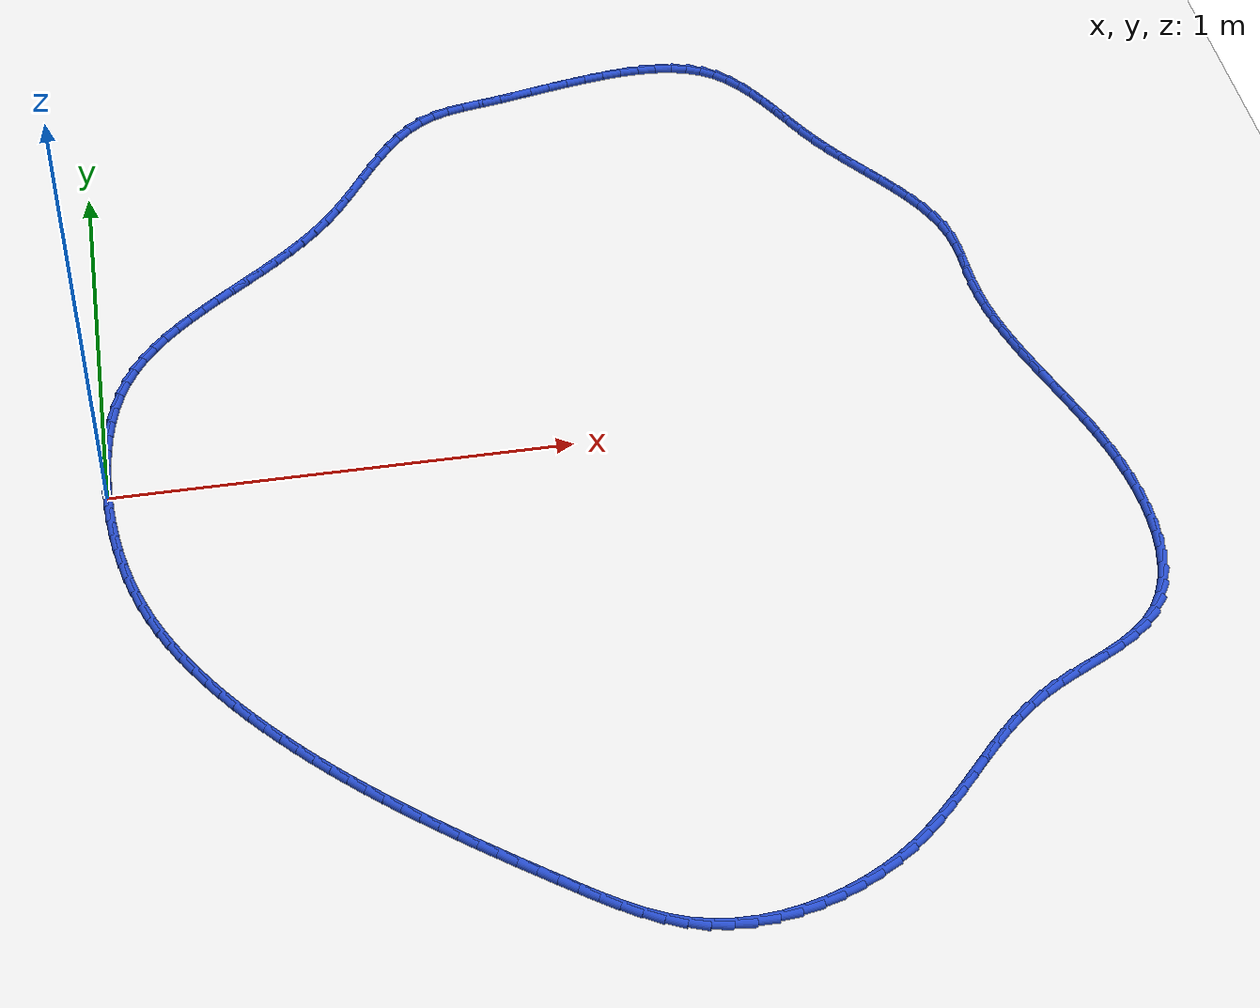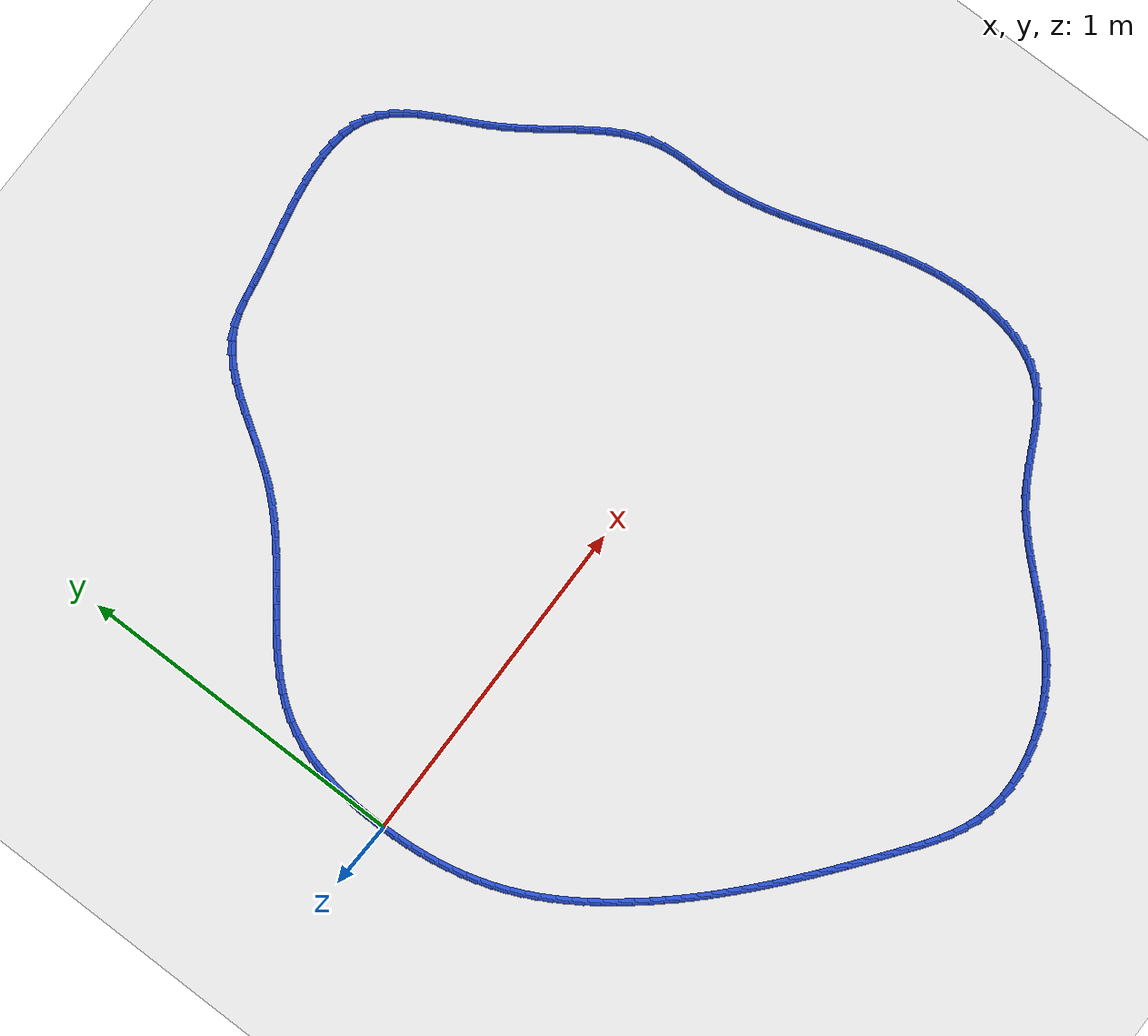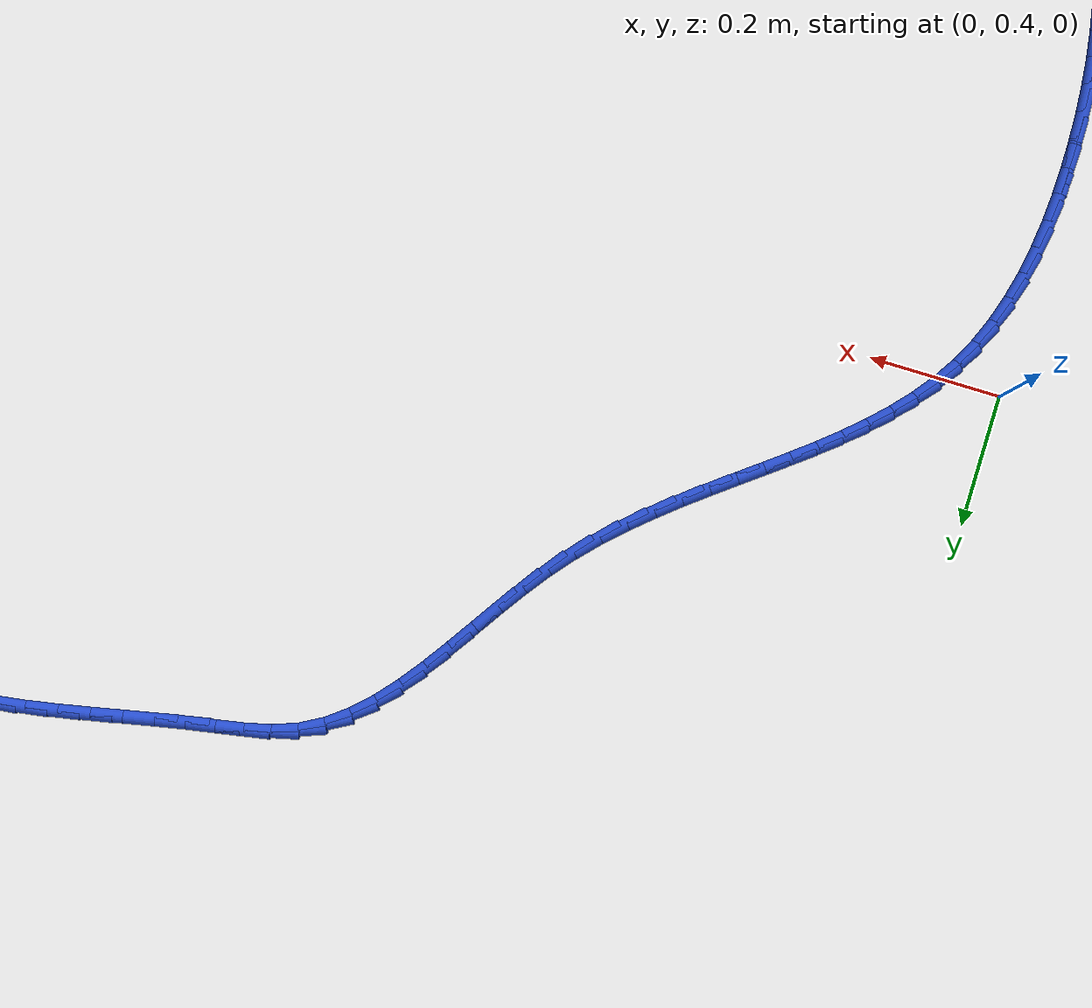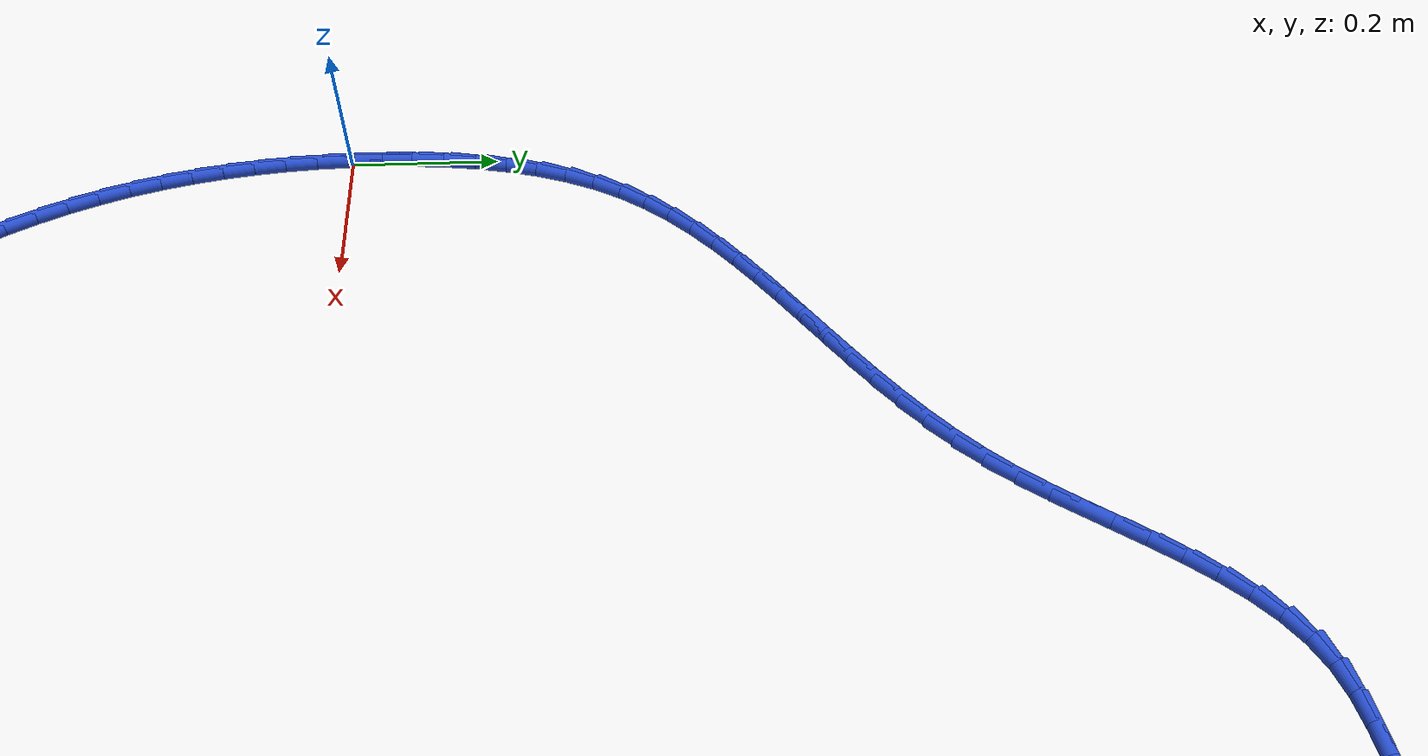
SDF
<sdf version="1.6">
 <world name="default">
  <light name="sun" type="directional">
   <pose>0 0 10 0 -0 0</pose>
   <diffuse>0.8 0.8 0.8 1</diffuse>
   <specular>0.2 0.2 0.2 1</specular>
   <attenuation>
    <range>1000</range>
    <constant>0.9</constant>
    <linear>0.01</linear>
    <quadratic>0.001</quadratic>
   </attenuation>
   <direction>-0.5 0.1 -0.9</direction>
  </light>
  <model name="ground_plane">
   <static>1</static>
   <link name="link">
    <collision name="collision">
     <geometry><plane><normal>0 0 1</normal><size>100 100</size></plane></geometry>
     <surface><friction><ode><mu>100</mu><mu2>50</mu2></ode></friction></surface>
    </collision>
    <visual name="visual">
     <cast_shadows>0</cast_shadows>
     <geometry><plane><normal>0 0 1</normal><size>100 100</size></plane></geometry>
     <material>
      <script><uri>file://media/materials/scripts/gazebo.material</uri><name>Gazebo/WhiteGlow</name></script>
     </material>
    </visual>
   </link>
  </model>
  <gravity>0 0 -9.8</gravity>
  <magnetic_field>6e-06 2.3e-05 -4.2e-05</magnetic_field>
  <atmosphere type="adiabatic"/>
  <physics name="default_physics" default="0" type="ode">
   <max_step_size>0.001</max_step_size>
   <real_time_factor>1</real_time_factor>
   <real_time_update_rate>1000</real_time_update_rate>
  </physics>
  <scene><ambient>0.4 0.4 0.4 1</ambient><background>0.7 0.7 0.7 1</background><shadows>1</shadows></scene>
  <spherical_coordinates>
   <surface_model>EARTH_WGS84</surface_model>
   <latitude_deg>0</latitude_deg>
   <longitude_deg>0</longitude_deg>
   <elevation>0</elevation>
   <heading_deg>0</heading_deg>
  </spherical_coordinates>
  <model name="line">
   <link name="link_0">
    <pose>1.214306433183765e-17 -6.938893903907228e-17 0.01 0 1.57 -1.5685302213631074</pose>
    <collision name="collision">
     <geometry><cylinder><radius>0.01</radius><length>0.08</length></cylinder></geometry>
    </collision>
    <visual name="visual">
     <material>
      <script><name>Gazebo/Blue</name><uri>file://media/materials/scripts/gazebo.material</uri></script>
     </material>
     <geometry><cylinder><radius>0.01</radius><length>0.08</length></cylinder></geometry>
    </visual>
   </link>
   <link name="link_1">
    <pose>-9.99671896477195e-05 0.044114019200969606 0.01 0 1.57 1.5363660218653532</pose>
    <collision name="collision">
     <geometry><cylinder><radius>0.01</radius><length>0.08</length></cylinder></geometry>
    </collision>
    <visual name="visual">
     <material>
      <script><name>Gazebo/Blue</name><uri>file://media/materials/scripts/gazebo.material</uri></script>
     </material>
     <geometry><cylinder><radius>0.01</radius><length>0.08</length></cylinder></geometry>
    </visual>
   </link>
   <link name="link_2">
    <pose>0.0014224744497002872 0.08831461527995998 0.01 0 1.57 1.4947771484701307</pose>
    <collision name="collision">
     <geometry><cylinder><radius>0.01</radius><length>0.08</length></cylinder></geometry>
    </collision>
    <visual name="visual">
     <material>
      <script><name>Gazebo/Blue</name><uri>file://media/materials/scripts/gazebo.material</uri></script>
     </material>
     <geometry><cylinder><radius>0.01</radius><length>0.08</length></cylinder></geometry>
    </visual>
   </link>
   <link name="link_3">
    <pose>0.004772150245150177 0.13229326493256127 0.01 0 1.57 1.447558426292112</pose>
    <collision name="collision">
     <geometry><cylinder><radius>0.01</radius><length>0.08</length></cylinder></geometry>
    </collision>
    <visual name="visual">
     <material>
      <script><name>Gazebo/Blue</name><uri>file://media/materials/scripts/gazebo.material</uri></script>
     </material>
     <geometry><cylinder><radius>0.01</radius><length>0.08</length></cylinder></geometry>
    </visual>
   </link>
   <link name="link_4">
    <pose>0.010153885523808115 0.17574144485436366 0.01 0 1.57 1.393863754703987</pose>
    <collision name="collision">
     <geometry><cylinder><radius>0.01</radius><length>0.08</length></cylinder></geometry>
    </collision>
    <visual name="visual">
     <material>
      <script><name>Gazebo/Blue</name><uri>file://media/materials/scripts/gazebo.material</uri></script>
     </material>
     <geometry><cylinder><radius>0.01</radius><length>0.08</length></cylinder></geometry>
    </visual>
   </link>
   <link name="link_5">
    <pose>0.01777250561278025 0.2183506317409575 0.01 0 1.57 1.3327550224882376</pose>
    <collision name="collision">
     <geometry><cylinder><radius>0.01</radius><length>0.08</length></cylinder></geometry>
    </collision>
    <visual name="visual">
     <material>
      <script><name>Gazebo/Blue</name><uri>file://media/materials/scripts/gazebo.material</uri></script>
     </material>
     <geometry><cylinder><radius>0.01</radius><length>0.08</length></cylinder></geometry>
    </visual>
   </link>
   <link name="link_6">
    <pose>0.02783283583917274 0.25981230228793284 0.01 0 1.57 1.26324750327836</pose>
    <collision name="collision">
     <geometry><cylinder><radius>0.01</radius><length>0.08</length></cylinder></geometry>
    </collision>
    <visual name="visual">
     <material>
      <script><name>Gazebo/Blue</name><uri>file://media/materials/scripts/gazebo.material</uri></script>
     </material>
     <geometry><cylinder><radius>0.01</radius><length>0.08</length></cylinder></geometry>
    </visual>
   </link>
   <link name="link_7">
    <pose>0.04053970153009172 0.29981793319087996 0.01 0 1.57 1.1844021716031738</pose>
    <collision name="collision">
     <geometry><cylinder><radius>0.01</radius><length>0.08</length></cylinder></geometry>
    </collision>
    <visual name="visual">
     <material>
      <script><name>Gazebo/Blue</name><uri>file://media/materials/scripts/gazebo.material</uri></script>
     </material>
     <geometry><cylinder><radius>0.01</radius><length>0.08</length></cylinder></geometry>
    </visual>
   </link>
   <link name="link_8">
    <pose>0.05609792801264335 0.33805900114538906 0.01 0 1.57 1.095634461560095</pose>
    <collision name="collision">
     <geometry><cylinder><radius>0.01</radius><length>0.08</length></cylinder></geometry>
    </collision>
    <visual name="visual">
     <material>
      <script><name>Gazebo/Blue</name><uri>file://media/materials/scripts/gazebo.material</uri></script>
     </material>
     <geometry><cylinder><radius>0.01</radius><length>0.08</length></cylinder></geometry>
    </visual>
   </link>
   <link name="link_9">
    <pose>0.07470799001230478 0.37423179226611597 0.01 0 1.57 1.004116747851904</pose>
    <collision name="collision">
     <geometry><cylinder><radius>0.01</radius><length>0.08</length></cylinder></geometry>
    </collision>
    <visual name="visual">
     <material>
      <script><name>Gazebo/Blue</name><uri>file://media/materials/scripts/gazebo.material</uri></script>
     </material>
     <geometry><cylinder><radius>0.01</radius><length>0.08</length></cylinder></geometry>
    </visual>
   </link>
   <link name="link_10">
    <pose>0.09636187944067819 0.408263062222364 0.01 0 1.57 0.9216298065416448</pose>
    <collision name="collision">
     <geometry><cylinder><radius>0.01</radius><length>0.08</length></cylinder></geometry>
    </collision>
    <visual name="visual">
     <material>
      <script><name>Gazebo/Blue</name><uri>file://media/materials/scripts/gazebo.material</uri></script>
     </material>
     <geometry><cylinder><radius>0.01</radius><length>0.08</length></cylinder></geometry>
    </visual>
   </link>
   <link name="link_11">
    <pose>0.12075550225557333 0.4404068780653176 0.01 0 1.57 0.850331340027047</pose>
    <collision name="collision">
     <geometry><cylinder><radius>0.01</radius><length>0.08</length></cylinder></geometry>
    </collision>
    <visual name="visual">
     <material>
      <script><name>Gazebo/Blue</name><uri>file://media/materials/scripts/gazebo.material</uri></script>
     </material>
     <geometry><cylinder><radius>0.01</radius><length>0.08</length></cylinder></geometry>
    </visual>
   </link>
   <link name="link_12">
    <pose>0.14756221451187218 0.47094223487734294 0.01 0 1.57 0.790780903514077</pose>
    <collision name="collision">
     <geometry><cylinder><radius>0.01</radius><length>0.08</length></cylinder></geometry>
    </collision>
    <visual name="visual">
     <material>
      <script><name>Gazebo/Blue</name><uri>file://media/materials/scripts/gazebo.material</uri></script>
     </material>
     <geometry><cylinder><radius>0.01</radius><length>0.08</length></cylinder></geometry>
    </visual>
   </link>
   <link name="link_13">
    <pose>0.17645537226445665 0.5001481277408066 0.01 0 1.57 0.7429546331523817</pose>
    <collision name="collision">
     <geometry><cylinder><radius>0.01</radius><length>0.08</length></cylinder></geometry>
    </collision>
    <visual name="visual">
     <material>
      <script><name>Gazebo/Blue</name><uri>file://media/materials/scripts/gazebo.material</uri></script>
     </material>
     <geometry><cylinder><radius>0.01</radius><length>0.08</length></cylinder></geometry>
    </visual>
   </link>
   <link name="link_14">
    <pose>0.20710833156820843 0.5283035517380745 0.01 0 1.57 0.7064945292356812</pose>
    <collision name="collision">
     <geometry><cylinder><radius>0.01</radius><length>0.08</length></cylinder></geometry>
    </collision>
    <visual name="visual">
     <material>
      <script><name>Gazebo/Blue</name><uri>file://media/materials/scripts/gazebo.material</uri></script>
     </material>
     <geometry><cylinder><radius>0.01</radius><length>0.08</length></cylinder></geometry>
    </visual>
   </link>
   <link name="link_15">
    <pose>0.2391944484780096 0.5556875019515133 0.01 0 1.57 0.680907797121899</pose>
    <collision name="collision">
     <geometry><cylinder><radius>0.01</radius><length>0.08</length></cylinder></geometry>
    </collision>
    <visual name="visual">
     <material>
      <script><name>Gazebo/Blue</name><uri>file://media/materials/scripts/gazebo.material</uri></script>
     </material>
     <geometry><cylinder><radius>0.01</radius><length>0.08</length></cylinder></geometry>
    </visual>
   </link>
   <link name="link_16">
    <pose>0.27238707904874204 0.582578973463489 0.01 0 1.57 0.6657018080436211</pose>
    <collision name="collision">
     <geometry><cylinder><radius>0.01</radius><length>0.08</length></cylinder></geometry>
    </collision>
    <visual name="visual">
     <material>
      <script><name>Gazebo/Blue</name><uri>file://media/materials/scripts/gazebo.material</uri></script>
     </material>
     <geometry><cylinder><radius>0.01</radius><length>0.08</length></cylinder></geometry>
    </visual>
   </link>
   <link name="link_17">
    <pose>0.3063595793352878 0.6092569613563683 0.01 0 1.57 0.6604625506550345</pose>
    <collision name="collision">
     <geometry><cylinder><radius>0.01</radius><length>0.08</length></cylinder></geometry>
    </collision>
    <visual name="visual">
     <material>
      <script><name>Gazebo/Blue</name><uri>file://media/materials/scripts/gazebo.material</uri></script>
     </material>
     <geometry><cylinder><radius>0.01</radius><length>0.08</length></cylinder></geometry>
    </visual>
   </link>
   <link name="link_18">
    <pose>0.34078530539252844 0.6360004607125169 0.01 0 1.57 0.6648904304787626</pose>
    <collision name="collision">
     <geometry><cylinder><radius>0.01</radius><length>0.08</length></cylinder></geometry>
    </collision>
    <visual name="visual">
     <material>
      <script><name>Gazebo/Blue</name><uri>file://media/materials/scripts/gazebo.material</uri></script>
     </material>
     <geometry><cylinder><radius>0.01</radius><length>0.08</length></cylinder></geometry>
    </visual>
   </link>
   <link name="link_19">
    <pose>0.3753376132753459 0.6630884666143015 0.01 0 1.57 0.6788050567709941</pose>
    <collision name="collision">
     <geometry><cylinder><radius>0.01</radius><length>0.08</length></cylinder></geometry>
    </collision>
    <visual name="visual">
     <material>
      <script><name>Gazebo/Blue</name><uri>file://media/materials/scripts/gazebo.material</uri></script>
     </material>
     <geometry><cylinder><radius>0.01</radius><length>0.08</length></cylinder></geometry>
    </visual>
   </link>
   <link name="link_20">
    <pose>0.40968985903862243 0.6907999741440884 0.01 0 1.57 0.7021258733396276</pose>
    <collision name="collision">
     <geometry><cylinder><radius>0.01</radius><length>0.08</length></cylinder></geometry>
    </collision>
    <visual name="visual">
     <material>
      <script><name>Gazebo/Blue</name><uri>file://media/materials/scripts/gazebo.material</uri></script>
     </material>
     <geometry><cylinder><radius>0.01</radius><length>0.08</length></cylinder></geometry>
    </visual>
   </link>
   <link name="link_21">
    <pose>0.4435153987372397 0.7194139783842439 0.01 0 1.57 0.7348309724507885</pose>
    <collision name="collision">
     <geometry><cylinder><radius>0.01</radius><length>0.08</length></cylinder></geometry>
    </collision>
    <visual name="visual">
     <material>
      <script><name>Gazebo/Blue</name><uri>file://media/materials/scripts/gazebo.material</uri></script>
     </material>
     <geometry><cylinder><radius>0.01</radius><length>0.08</length></cylinder></geometry>
    </visual>
   </link>
   <link name="link_22">
    <pose>0.4764875884260793 0.7492094744171338 0.01 0 1.57 0.7768935577189008</pose>
    <collision name="collision">
     <geometry><cylinder><radius>0.01</radius><length>0.08</length></cylinder></geometry>
    </collision>
    <visual name="visual">
     <material>
      <script><name>Gazebo/Blue</name><uri>file://media/materials/scripts/gazebo.material</uri></script>
     </material>
     <geometry><cylinder><radius>0.01</radius><length>0.08</length></cylinder></geometry>
    </visual>
   </link>
   <link name="link_23">
    <pose>0.5082797841600237 0.7804654573251251 0.01 0 1.57 0.8281953911116935</pose>
    <collision name="collision">
     <geometry><cylinder><radius>0.01</radius><length>0.08</length></cylinder></geometry>
    </collision>
    <visual name="visual">
     <material>
      <script><name>Gazebo/Blue</name><uri>file://media/materials/scripts/gazebo.material</uri></script>
     </material>
     <geometry><cylinder><radius>0.01</radius><length>0.08</length></cylinder></geometry>
    </visual>
   </link>
   <link name="link_24">
    <pose>0.5385653419939547 0.813460922190584 0.01 0 1.57 0.8878043707804502</pose>
    <collision name="collision">
     <geometry><cylinder><radius>0.01</radius><length>0.08</length></cylinder></geometry>
    </collision>
    <visual name="visual">
     <material>
      <script><name>Gazebo/Blue</name><uri>file://media/materials/scripts/gazebo.material</uri></script>
     </material>
     <geometry><cylinder><radius>0.01</radius><length>0.08</length></cylinder></geometry>
    </visual>
   </link>
   <link name="link_25">
    <pose>0.5670356861177517 0.8484530291755793 0.01 0 1.57 0.9416291684233294</pose>
    <collision name="collision">
     <geometry><cylinder><radius>0.01</radius><length>0.08</length></cylinder></geometry>
    </collision>
    <visual name="visual">
     <material>
      <script><name>Gazebo/Blue</name><uri>file://media/materials/scripts/gazebo.material</uri></script>
     </material>
     <geometry><cylinder><radius>0.01</radius><length>0.08</length></cylinder></geometry>
    </visual>
   </link>
   <link name="link_26">
    <pose>0.5937879195670831 0.8852086850062272 0.01 0 1.57 0.9767766220533224</pose>
    <collision name="collision">
     <geometry><cylinder><radius>0.01</radius><length>0.08</length></cylinder></geometry>
    </collision>
    <visual name="visual">
     <material>
      <script><name>Gazebo/Blue</name><uri>file://media/materials/scripts/gazebo.material</uri></script>
     </material>
     <geometry><cylinder><radius>0.01</radius><length>0.08</length></cylinder></geometry>
    </visual>
   </link>
   <link name="link_27">
    <pose>0.6193194056220332 0.923011091226237 0.01 0 1.57 0.9934552692911446</pose>
    <collision name="collision">
     <geometry><cylinder><radius>0.01</radius><length>0.08</length></cylinder></geometry>
    </collision>
    <visual name="visual">
     <material>
      <script><name>Gazebo/Blue</name><uri>file://media/materials/scripts/gazebo.material</uri></script>
     </material>
     <geometry><cylinder><radius>0.01</radius><length>0.08</length></cylinder></geometry>
    </visual>
   </link>
   <link name="link_28">
    <pose>0.6441444919159811 0.9611229241839668 0.01 0 1.57 0.9918421998247919</pose>
    <collision name="collision">
     <geometry><cylinder><radius>0.01</radius><length>0.08</length></cylinder></geometry>
    </collision>
    <visual name="visual">
     <material>
      <script><name>Gazebo/Blue</name><uri>file://media/materials/scripts/gazebo.material</uri></script>
     </material>
     <geometry><cylinder><radius>0.01</radius><length>0.08</length></cylinder></geometry>
    </visual>
   </link>
   <link name="link_29">
    <pose>0.668777526082305 0.9988068602277739 0.01 0 1.57 0.9713275255370154</pose>
    <collision name="collision">
     <geometry><cylinder><radius>0.01</radius><length>0.08</length></cylinder></geometry>
    </collision>
    <visual name="visual">
     <material>
      <script><name>Gazebo/Blue</name><uri>file://media/materials/scripts/gazebo.material</uri></script>
     </material>
     <geometry><cylinder><radius>0.01</radius><length>0.08</length></cylinder></geometry>
    </visual>
   </link>
   <link name="link_30">
    <pose>0.6937328557543836 1.035325575706015 0.01 0 1.57 0.9304485648295</pose>
    <collision name="collision">
     <geometry><cylinder><radius>0.01</radius><length>0.08</length></cylinder></geometry>
    </collision>
    <visual name="visual">
     <material>
      <script><name>Gazebo/Blue</name><uri>file://media/materials/scripts/gazebo.material</uri></script>
     </material>
     <geometry><cylinder><radius>0.01</radius><length>0.08</length></cylinder></geometry>
    </visual>
   </link>
   <link name="link_31">
    <pose>0.7195248285655957 1.0699417469670487 0.01 0 1.57 0.866972485142294</pose>
    <collision name="collision">
     <geometry><cylinder><radius>0.01</radius><length>0.08</length></cylinder></geometry>
    </collision>
    <visual name="visual">
     <material>
      <script><name>Gazebo/Blue</name><uri>file://media/materials/scripts/gazebo.material</uri></script>
     </material>
     <geometry><cylinder><radius>0.01</radius><length>0.08</length></cylinder></geometry>
    </visual>
   </link>
   <link name="link_32">
    <pose>0.7466677921493202 1.1019180503592323 0.01 0 1.57 0.7782952020079401</pose>
    <collision name="collision">
     <geometry><cylinder><radius>0.01</radius><length>0.08</length></cylinder></geometry>
    </collision>
    <visual name="visual">
     <material>
      <script><name>Gazebo/Blue</name><uri>file://media/materials/scripts/gazebo.material</uri></script>
     </material>
     <geometry><cylinder><radius>0.01</radius><length>0.08</length></cylinder></geometry>
    </visual>
   </link>
   <link name="link_33">
    <pose>0.7756760941389356 1.1305171622309234 0.01 0 1.57 0.662465236075716</pose>
    <collision name="collision">
     <geometry><cylinder><radius>0.01</radius><length>0.08</length></cylinder></geometry>
    </collision>
    <visual name="visual">
     <material>
      <script><name>Gazebo/Blue</name><uri>file://media/materials/scripts/gazebo.material</uri></script>
     </material>
     <geometry><cylinder><radius>0.01</radius><length>0.08</length></cylinder></geometry>
    </visual>
   </link>
   <link name="link_34">
    <pose>0.8070640821678203 1.1550017589304789 0.01 0 1.57 0.5200918389951178</pose>
    <collision name="collision">
     <geometry><cylinder><radius>0.01</radius><length>0.08</length></cylinder></geometry>
    </collision>
    <visual name="visual">
     <material>
      <script><name>Gazebo/Blue</name><uri>file://media/materials/scripts/gazebo.material</uri></script>
     </material>
     <geometry><cylinder><radius>0.01</radius><length>0.08</length></cylinder></geometry>
    </visual>
   </link>
   <link name="link_35">
    <pose>0.8413461038693528 1.1746345168062564 0.01 0 1.57 0.36163210237958193</pose>
    <collision name="collision">
     <geometry><cylinder><radius>0.01</radius><length>0.08</length></cylinder></geometry>
    </collision>
    <visual name="visual">
     <material>
      <script><name>Gazebo/Blue</name><uri>file://media/materials/scripts/gazebo.material</uri></script>
     </material>
     <geometry><cylinder><radius>0.01</radius><length>0.08</length></cylinder></geometry>
    </visual>
   </link>
   <link name="link_36">
    <pose>0.8789596154095368 1.1888624796099996 0.01 0 1.57 0.242095698993893</pose>
    <collision name="collision">
     <geometry><cylinder><radius>0.01</radius><length>0.08</length></cylinder></geometry>
    </collision>
    <visual name="visual">
     <material>
      <script><name>Gazebo/Blue</name><uri>file://media/materials/scripts/gazebo.material</uri></script>
     </material>
     <geometry><cylinder><radius>0.01</radius><length>0.08</length></cylinder></geometry>
    </visual>
   </link>
   <link name="link_37">
    <pose>0.9196052284112275 1.1988994686014702 0.01 0 1.57 0.18504675685482516</pose>
    <collision name="collision">
     <geometry><cylinder><radius>0.01</radius><length>0.08</length></cylinder></geometry>
    </collision>
    <visual name="visual">
     <material>
      <script><name>Gazebo/Blue</name><uri>file://media/materials/scripts/gazebo.material</uri></script>
     </material>
     <geometry><cylinder><radius>0.01</radius><length>0.08</length></cylinder></geometry>
    </visual>
   </link>
   <link name="link_38">
    <pose>0.9625734591464802 1.2069426159011527 0.01 0 1.57 0.18227392945360685</pose>
    <collision name="collision">
     <geometry><cylinder><radius>0.01</radius><length>0.08</length></cylinder></geometry>
    </collision>
    <visual name="visual">
     <material>
      <script><name>Gazebo/Blue</name><uri>file://media/materials/scripts/gazebo.material</uri></script>
     </material>
     <geometry><cylinder><radius>0.01</radius><length>0.08</length></cylinder></geometry>
    </visual>
   </link>
   <link name="link_39">
    <pose>1.00715563410935 1.2151599904175578 0.01 0 1.57 0.20176720868793951</pose>
    <collision name="collision">
     <geometry><cylinder><radius>0.01</radius><length>0.08</length></cylinder></geometry>
    </collision>
    <visual name="visual">
     <material>
      <script><name>Gazebo/Blue</name><uri>file://media/materials/scripts/gazebo.material</uri></script>
     </material>
     <geometry><cylinder><radius>0.01</radius><length>0.08</length></cylinder></geometry>
    </visual>
   </link>
   <link name="link_40">
    <pose>1.052804278565127 1.2244974444895582 0.01 0 1.57 0.21204068017003128</pose>
    <collision name="collision">
     <geometry><cylinder><radius>0.01</radius><length>0.08</length></cylinder></geometry>
    </collision>
    <visual name="visual">
     <material>
      <script><name>Gazebo/Blue</name><uri>file://media/materials/scripts/gazebo.material</uri></script>
     </material>
     <geometry><cylinder><radius>0.01</radius><length>0.08</length></cylinder></geometry>
    </visual>
   </link>
   <link name="link_41">
    <pose>1.0991597471132428 1.234476699721727 0.01 0 1.57 0.21216668842118025</pose>
    <collision name="collision">
     <geometry><cylinder><radius>0.01</radius><length>0.08</length></cylinder></geometry>
    </collision>
    <visual name="visual">
     <material>
      <script><name>Gazebo/Blue</name><uri>file://media/materials/scripts/gazebo.material</uri></script>
     </material>
     <geometry><cylinder><radius>0.01</radius><length>0.08</length></cylinder></geometry>
    </visual>
   </link>
   <link name="link_42">
    <pose>1.1458729908159389 1.2445391348454946 0.01 0 1.57 0.2023832428279299</pose>
    <collision name="collision">
     <geometry><cylinder><radius>0.01</radius><length>0.08</length></cylinder></geometry>
    </collision>
    <visual name="visual">
     <material>
      <script><name>Gazebo/Blue</name><uri>file://media/materials/scripts/gazebo.material</uri></script>
     </material>
     <geometry><cylinder><radius>0.01</radius><length>0.08</length></cylinder></geometry>
    </visual>
   </link>
   <link name="link_43">
    <pose>1.1925949607354576 1.2541261285922911 0.01 0 1.57 0.18235479887713393</pose>
    <collision name="collision">
     <geometry><cylinder><radius>0.01</radius><length>0.08</length></cylinder></geometry>
    </collision>
    <visual name="visual">
     <material>
      <script><name>Gazebo/Blue</name><uri>file://media/materials/scripts/gazebo.material</uri></script>
     </material>
     <geometry><cylinder><radius>0.01</radius><length>0.08</length></cylinder></geometry>
    </visual>
   </link>
   <link name="link_44">
    <pose>1.2389766079340412 1.2626790596935467 0.01 0 1.57 0.15116667134634432</pose>
    <collision name="collision">
     <geometry><cylinder><radius>0.01</radius><length>0.08</length></cylinder></geometry>
    </collision>
    <visual name="visual">
     <material>
      <script><name>Gazebo/Blue</name><uri>file://media/materials/scripts/gazebo.material</uri></script>
     </material>
     <geometry><cylinder><radius>0.01</radius><length>0.08</length></cylinder></geometry>
    </visual>
   </link>
   <link name="link_45">
    <pose>1.2846688834739328 1.269639306880691 0.01 0 1.57 0.10728030164639592</pose>
    <collision name="collision">
     <geometry><cylinder><radius>0.01</radius><length>0.08</length></cylinder></geometry>
    </collision>
    <visual name="visual">
     <material>
      <script><name>Gazebo/Blue</name><uri>file://media/materials/scripts/gazebo.material</uri></script>
     </material>
     <geometry><cylinder><radius>0.01</radius><length>0.08</length></cylinder></geometry>
    </visual>
   </link>
   <link name="link_46">
    <pose>1.329322738417373 1.2744482488851545 0.01 0 1.57 0.048475765123383675</pose>
    <collision name="collision">
     <geometry><cylinder><radius>0.01</radius><length>0.08</length></cylinder></geometry>
    </collision>
    <visual name="visual">
     <material>
      <script><name>Gazebo/Blue</name><uri>file://media/materials/scripts/gazebo.material</uri></script>
     </material>
     <geometry><cylinder><radius>0.01</radius><length>0.08</length></cylinder></geometry>
    </visual>
   </link>
   <link name="link_47">
    <pose>1.3725891238266061 1.2765472644383677 0.01 0 1.57 -0.028153789841341887</pose>
    <collision name="collision">
     <geometry><cylinder><radius>0.01</radius><length>0.08</length></cylinder></geometry>
    </collision>
    <visual name="visual">
     <material>
      <script><name>Gazebo/Blue</name><uri>file://media/materials/scripts/gazebo.material</uri></script>
     </material>
     <geometry><cylinder><radius>0.01</radius><length>0.08</length></cylinder></geometry>
    </visual>
   </link>
   <link name="link_48">
    <pose>1.4141189907638725 1.2753777322717603 0.01 0 1.57 -0.12600624215034267</pose>
    <collision name="collision">
     <geometry><cylinder><radius>0.01</radius><length>0.08</length></cylinder></geometry>
    </collision>
    <visual name="visual">
     <material>
      <script><name>Gazebo/Blue</name><uri>file://media/materials/scripts/gazebo.material</uri></script>
     </material>
     <geometry><cylinder><radius>0.01</radius><length>0.08</length></cylinder></geometry>
    </visual>
   </link>
   <link name="link_49">
    <pose>1.4535632902914153 1.2703810311167623 0.01 0 1.57 -0.2482836849005246</pose>
    <collision name="collision">
     <geometry><cylinder><radius>0.01</radius><length>0.08</length></cylinder></geometry>
    </collision>
    <visual name="visual">
     <material>
      <script><name>Gazebo/Blue</name><uri>file://media/materials/scripts/gazebo.material</uri></script>
     </material>
     <geometry><cylinder><radius>0.01</radius><length>0.08</length></cylinder></geometry>
    </visual>
   </link>
   <link name="link_50">
    <pose>1.4905729734714768 1.2609985397048038 0.01 0 1.57 -0.39643463672519014</pose>
    <collision name="collision">
     <geometry><cylinder><radius>0.01</radius><length>0.08</length></cylinder></geometry>
    </collision>
    <visual name="visual">
     <material>
      <script><name>Gazebo/Blue</name><uri>file://media/materials/scripts/gazebo.material</uri></script>
     </material>
     <geometry><cylinder><radius>0.01</radius><length>0.08</length></cylinder></geometry>
    </visual>
   </link>
   <link name="link_51">
    <pose>1.5247989913662994 1.2466716367673156 0.01 0 1.57 -0.5675971210926255</pose>
    <collision name="collision">
     <geometry><cylinder><radius>0.01</radius><length>0.08</length></cylinder></geometry>
    </collision>
    <visual name="visual">
     <material>
      <script><name>Gazebo/Blue</name><uri>file://media/materials/scripts/gazebo.material</uri></script>
     </material>
     <geometry><cylinder><radius>0.01</radius><length>0.08</length></cylinder></geometry>
    </visual>
   </link>
   <link name="link_52">
    <pose>1.555894793586734 1.2268454607813906 0.01 0 1.57 -0.7385750831857838</pose>
    <collision name="collision">
     <geometry><cylinder><radius>0.01</radius><length>0.08</length></cylinder></geometry>
    </collision>
    <visual name="visual">
     <material>
      <script><name>Gazebo/Blue</name><uri>file://media/materials/scripts/gazebo.material</uri></script>
     </material>
     <geometry><cylinder><radius>0.01</radius><length>0.08</length></cylinder></geometry>
    </visual>
   </link>
   <link name="link_53">
    <pose>1.5838176200997682 1.20142228540653 0.01 0 1.57 -0.8739698385360467</pose>
    <collision name="collision">
     <geometry><cylinder><radius>0.01</radius><length>0.08</length></cylinder></geometry>
    </collision>
    <visual name="visual">
     <material>
      <script><name>Gazebo/Blue</name><uri>file://media/materials/scripts/gazebo.material</uri></script>
     </material>
     <geometry><cylinder><radius>0.01</radius><length>0.08</length></cylinder></geometry>
    </visual>
   </link>
   <link name="link_54">
    <pose>1.6091155070602459 1.1711933977868496 0.01 0 1.57 -0.9721572210861517</pose>
    <collision name="collision">
     <geometry><cylinder><radius>0.01</radius><length>0.08</length></cylinder></geometry>
    </collision>
    <visual name="visual">
     <material>
      <script><name>Gazebo/Blue</name><uri>file://media/materials/scripts/gazebo.material</uri></script>
     </material>
     <geometry><cylinder><radius>0.01</radius><length>0.08</length></cylinder></geometry>
    </visual>
   </link>
   <link name="link_55">
    <pose>1.632404479735785 1.1370523931708585 0.01 0 1.57 -1.038322078686913</pose>
    <collision name="collision">
     <geometry><cylinder><radius>0.01</radius><length>0.08</length></cylinder></geometry>
    </collision>
    <visual name="visual">
     <material>
      <script><name>Gazebo/Blue</name><uri>file://media/materials/scripts/gazebo.material</uri></script>
     </material>
     <geometry><cylinder><radius>0.01</radius><length>0.08</length></cylinder></geometry>
    </visual>
   </link>
   <link name="link_56">
    <pose>1.6543005633940018 1.0998928668070662 0.01 0 1.57 -1.0775251012836669</pose>
    <collision name="collision">
     <geometry><cylinder><radius>0.01</radius><length>0.08</length></cylinder></geometry>
    </collision>
    <visual name="visual">
     <material>
      <script><name>Gazebo/Blue</name><uri>file://media/materials/scripts/gazebo.material</uri></script>
     </material>
     <geometry><cylinder><radius>0.01</radius><length>0.08</length></cylinder></geometry>
    </visual>
   </link>
   <link name="link_57">
    <pose>1.6754197833025146 1.0606084139439822 0.01 0 1.57 -1.093413142505255</pose>
    <collision name="collision">
     <geometry><cylinder><radius>0.01</radius><length>0.08</length></cylinder></geometry>
    </collision>
    <visual name="visual">
     <material>
      <script><name>Gazebo/Blue</name><uri>file://media/materials/scripts/gazebo.material</uri></script>
     </material>
     <geometry><cylinder><radius>0.01</radius><length>0.08</length></cylinder></geometry>
    </visual>
   </link>
   <link name="link_58">
    <pose>1.6963781647289409 1.0200926298301154 0.01 0 1.57 -1.0880121415725734</pose>
    <collision name="collision">
     <geometry><cylinder><radius>0.01</radius><length>0.08</length></cylinder></geometry>
    </collision>
    <visual name="visual">
     <material>
      <script><name>Gazebo/Blue</name><uri>file://media/materials/scripts/gazebo.material</uri></script>
     </material>
     <geometry><cylinder><radius>0.01</radius><length>0.08</length></cylinder></geometry>
    </visual>
   </link>
   <link name="link_59">
    <pose>1.717791732940897 0.979239109713976 0.01 0 1.57 -1.061856711473339</pose>
    <collision name="collision">
     <geometry><cylinder><radius>0.01</radius><length>0.08</length></cylinder></geometry>
    </collision>
    <visual name="visual">
     <material>
      <script><name>Gazebo/Blue</name><uri>file://media/materials/scripts/gazebo.material</uri></script>
     </material>
     <geometry><cylinder><radius>0.01</radius><length>0.08</length></cylinder></geometry>
    </visual>
   </link>
   <link name="link_60">
    <pose>1.7402765132060012 0.938941448844073 0.01 0 1.57 -1.0175725071554629</pose>
    <collision name="collision">
     <geometry><cylinder><radius>0.01</radius><length>0.08</length></cylinder></geometry>
    </collision>
    <visual name="visual">
     <material>
      <script><name>Gazebo/Blue</name><uri>file://media/materials/scripts/gazebo.material</uri></script>
     </material>
     <geometry><cylinder><radius>0.01</radius><length>0.08</length></cylinder></geometry>
    </visual>
   </link>
   <link name="link_61">
    <pose>1.7643358898525563 0.8999820287479273 0.01 0 1.57 -0.9775227770807143</pose>
    <collision name="collision">
     <geometry><cylinder><radius>0.01</radius><length>0.08</length></cylinder></geometry>
    </collision>
    <visual name="visual">
     <material>
      <script><name>Gazebo/Blue</name><uri>file://media/materials/scripts/gazebo.material</uri></script>
     </material>
     <geometry><cylinder><radius>0.01</radius><length>0.08</length></cylinder></geometry>
    </visual>
   </link>
   <link name="link_62">
    <pose>1.7896948102922994 0.8623746572304636 0.01 0 1.57 -0.9517084450020616</pose>
    <collision name="collision">
     <geometry><cylinder><radius>0.01</radius><length>0.08</length></cylinder></geometry>
    </collision>
    <visual name="visual">
     <material>
      <script><name>Gazebo/Blue</name><uri>file://media/materials/scripts/gazebo.material</uri></script>
     </material>
     <geometry><cylinder><radius>0.01</radius><length>0.08</length></cylinder></geometry>
    </visual>
   </link>
   <link name="link_63">
    <pose>1.8157494060300217 0.8258084924554162 0.01 0 1.57 -0.940505118203751</pose>
    <collision name="collision">
     <geometry><cylinder><radius>0.01</radius><length>0.08</length></cylinder></geometry>
    </collision>
    <visual name="visual">
     <material>
      <script><name>Gazebo/Blue</name><uri>file://media/materials/scripts/gazebo.material</uri></script>
     </material>
     <geometry><cylinder><radius>0.01</radius><length>0.08</length></cylinder></geometry>
    </visual>
   </link>
   <link name="link_64">
    <pose>1.8418946423705556 0.7899715411629128 0.01 0 1.57 -0.944385558358054</pose>
    <collision name="collision">
     <geometry><cylinder><radius>0.01</radius><length>0.08</length></cylinder></geometry>
    </collision>
    <visual name="visual">
     <material>
      <script><name>Gazebo/Blue</name><uri>file://media/materials/scripts/gazebo.material</uri></script>
     </material>
     <geometry><cylinder><radius>0.01</radius><length>0.08</length></cylinder></geometry>
    </visual>
   </link>
   <link name="link_65">
    <pose>1.8675254846187321 0.7545518100930788 0.01 0 1.57 -0.964048414507617</pose>
    <collision name="collision">
     <geometry><cylinder><radius>0.01</radius><length>0.08</length></cylinder></geometry>
    </collision>
    <visual name="visual">
     <material>
      <script><name>Gazebo/Blue</name><uri>file://media/materials/scripts/gazebo.material</uri></script>
     </material>
     <geometry><cylinder><radius>0.01</radius><length>0.08</length></cylinder></geometry>
    </visual>
   </link>
   <link name="link_66">
    <pose>1.8920368980793856 0.7192373059860411 0.01 0 1.57 -1.000418631432097</pose>
    <collision name="collision">
     <geometry><cylinder><radius>0.01</radius><length>0.08</length></cylinder></geometry>
    </collision>
    <visual name="visual">
     <material>
      <script><name>Gazebo/Blue</name><uri>file://media/materials/scripts/gazebo.material</uri></script>
     </material>
     <geometry><cylinder><radius>0.01</radius><length>0.08</length></cylinder></geometry>
    </visual>
   </link>
   <link name="link_67">
    <pose>1.914823848057346 0.683716035581926 0.01 0 1.57 -1.0545173957215481</pose>
    <collision name="collision">
     <geometry><cylinder><radius>0.01</radius><length>0.08</length></cylinder></geometry>
    </collision>
    <visual name="visual">
     <material>
      <script><name>Gazebo/Blue</name><uri>file://media/materials/scripts/gazebo.material</uri></script>
     </material>
     <geometry><cylinder><radius>0.01</radius><length>0.08</length></cylinder></geometry>
    </visual>
   </link>
   <link name="link_68">
    <pose>1.935281299857446 0.6476760056208598 0.01 0 1.57 -1.1271422756204768</pose>
    <collision name="collision">
     <geometry><cylinder><radius>0.01</radius><length>0.08</length></cylinder></geometry>
    </collision>
    <visual name="visual">
     <material>
      <script><name>Gazebo/Blue</name><uri>file://media/materials/scripts/gazebo.material</uri></script>
     </material>
     <geometry><cylinder><radius>0.01</radius><length>0.08</length></cylinder></geometry>
    </visual>
   </link>
   <link name="link_69">
    <pose>1.952804218784519 0.6108052228429699 0.01 0 1.57 -1.2183071044696931</pose>
    <collision name="collision">
     <geometry><cylinder><radius>0.01</radius><length>0.08</length></cylinder></geometry>
    </collision>
    <visual name="visual">
     <material>
      <script><name>Gazebo/Blue</name><uri>file://media/materials/scripts/gazebo.material</uri></script>
     </material>
     <geometry><cylinder><radius>0.01</radius><length>0.08</length></cylinder></geometry>
    </visual>
   </link>
   <link name="link_70">
    <pose>1.9667875701433961 0.572791693988382 0.01 0 1.57 -1.3264930590613038</pose>
    <collision name="collision">
     <geometry><cylinder><radius>0.01</radius><length>0.08</length></cylinder></geometry>
    </collision>
    <visual name="visual">
     <material>
      <script><name>Gazebo/Blue</name><uri>file://media/materials/scripts/gazebo.material</uri></script>
     </material>
     <geometry><cylinder><radius>0.01</radius><length>0.08</length></cylinder></geometry>
    </visual>
   </link>
   <link name="link_71">
    <pose>1.9766263192389097 0.5333234257972227 0.01 0 1.57 -1.4419387446465755</pose>
    <collision name="collision">
     <geometry><cylinder><radius>0.01</radius><length>0.08</length></cylinder></geometry>
    </collision>
    <visual name="visual">
     <material>
      <script><name>Gazebo/Blue</name><uri>file://media/materials/scripts/gazebo.material</uri></script>
     </material>
     <geometry><cylinder><radius>0.01</radius><length>0.08</length></cylinder></geometry>
    </visual>
   </link>
   <link name="link_72">
    <pose>1.9819571176885418 0.49218295920234606 0.01 0 1.57 -1.5231686455971853</pose>
    <collision name="collision">
     <geometry><cylinder><radius>0.01</radius><length>0.08</length></cylinder></geometry>
    </collision>
    <visual name="visual">
     <material>
      <script><name>Gazebo/Blue</name><uri>file://media/materials/scripts/gazebo.material</uri></script>
     </material>
     <geometry><cylinder><radius>0.01</radius><length>0.08</length></cylinder></geometry>
    </visual>
   </link>
   <link name="link_73">
    <pose>1.9839789662794418 0.449763938909481 0.01 0 1.57 -1.5584136674722113</pose>
    <collision name="collision">
     <geometry><cylinder><radius>0.01</radius><length>0.08</length></cylinder></geometry>
    </collision>
    <visual name="visual">
     <material>
      <script><name>Gazebo/Blue</name><uri>file://media/materials/scripts/gazebo.material</uri></script>
     </material>
     <geometry><cylinder><radius>0.01</radius><length>0.08</length></cylinder></geometry>
    </visual>
   </link>
   <link name="link_74">
    <pose>1.9845122019544488 0.40670304164071797 0.01 0 1.57 -1.550677419740935</pose>
    <collision name="collision">
     <geometry><cylinder><radius>0.01</radius><length>0.08</length></cylinder></geometry>
    </collision>
    <visual name="visual">
     <material>
      <script><name>Gazebo/Blue</name><uri>file://media/materials/scripts/gazebo.material</uri></script>
     </material>
     <geometry><cylinder><radius>0.01</radius><length>0.08</length></cylinder></geometry>
    </visual>
   </link>
   <link name="link_75">
    <pose>1.9853787491954322 0.36363756507478934 0.01 0 1.57 -1.5032516878962703</pose>
    <collision name="collision">
     <geometry><cylinder><radius>0.01</radius><length>0.08</length></cylinder></geometry>
    </collision>
    <visual name="visual">
     <material>
      <script><name>Gazebo/Blue</name><uri>file://media/materials/scripts/gazebo.material</uri></script>
     </material>
     <geometry><cylinder><radius>0.01</radius><length>0.08</length></cylinder></geometry>
    </visual>
   </link>
   <link name="link_76">
    <pose>1.988252765826624 0.3211524077002992 0.01 0 1.57 -1.445558984806441</pose>
    <collision name="collision">
     <geometry><cylinder><radius>0.01</radius><length>0.08</length></cylinder></geometry>
    </collision>
    <visual name="visual">
     <material>
      <script><name>Gazebo/Blue</name><uri>file://media/materials/scripts/gazebo.material</uri></script>
     </material>
     <geometry><cylinder><radius>0.01</radius><length>0.08</length></cylinder></geometry>
    </visual>
   </link>
   <link name="link_77">
    <pose>1.9935126386917486 0.279372977677972 0.01 0 1.57 -1.3941318600142136</pose>
    <collision name="collision">
     <geometry><cylinder><radius>0.01</radius><length>0.08</length></cylinder></geometry>
    </collision>
    <visual name="visual">
     <material>
      <script><name>Gazebo/Blue</name><uri>file://media/materials/scripts/gazebo.material</uri></script>
     </material>
     <geometry><cylinder><radius>0.01</radius><length>0.08</length></cylinder></geometry>
    </visual>
   </link>
   <link name="link_78">
    <pose>2.0008654561242056 0.23818663556810374 0.01 0 1.57 -1.349764823086508</pose>
    <collision name="collision">
     <geometry><cylinder><radius>0.01</radius><length>0.08</length></cylinder></geometry>
    </collision>
    <visual name="visual">
     <material>
      <script><name>Gazebo/Blue</name><uri>file://media/materials/scripts/gazebo.material</uri></script>
     </material>
     <geometry><cylinder><radius>0.01</radius><length>0.08</length></cylinder></geometry>
    </visual>
   </link>
   <link name="link_79">
    <pose>2.0100126345737253 0.19747873063753887 0.01 0 1.57 -1.312868076178453</pose>
    <collision name="collision">
     <geometry><cylinder><radius>0.01</radius><length>0.08</length></cylinder></geometry>
    </collision>
    <visual name="visual">
     <material>
      <script><name>Gazebo/Blue</name><uri>file://media/materials/scripts/gazebo.material</uri></script>
     </material>
     <geometry><cylinder><radius>0.01</radius><length>0.08</length></cylinder></geometry>
    </visual>
   </link>
   <link name="link_80">
    <pose>2.0206555904900383 0.15713461215312305 0.01 0 1.57 -1.2836546905165451</pose>
    <collision name="collision">
     <geometry><cylinder><radius>0.01</radius><length>0.08</length></cylinder></geometry>
    </collision>
    <visual name="visual">
     <material>
      <script><name>Gazebo/Blue</name><uri>file://media/materials/scripts/gazebo.material</uri></script>
     </material>
     <geometry><cylinder><radius>0.01</radius><length>0.08</length></cylinder></geometry>
    </visual>
   </link>
   <link name="link_81">
    <pose>2.032495740322876 0.117039629381701 0.01 0 1.57 -1.2621969811278928</pose>
    <collision name="collision">
     <geometry><cylinder><radius>0.01</radius><length>0.08</length></cylinder></geometry>
    </collision>
    <visual name="visual">
     <material>
      <script><name>Gazebo/Blue</name><uri>file://media/materials/scripts/gazebo.material</uri></script>
     </material>
     <geometry><cylinder><radius>0.01</radius><length>0.08</length></cylinder></geometry>
    </visual>
   </link>
   <link name="link_82">
    <pose>2.0452345005219694 0.07707913159011748 0.01 0 1.57 -1.2484773055154104</pose>
    <collision name="collision">
     <geometry><cylinder><radius>0.01</radius><length>0.08</length></cylinder></geometry>
    </collision>
    <visual name="visual">
     <material>
      <script><name>Gazebo/Blue</name><uri>file://media/materials/scripts/gazebo.material</uri></script>
     </material>
     <geometry><cylinder><radius>0.01</radius><length>0.08</length></cylinder></geometry>
    </visual>
   </link>
   <link name="link_83">
    <pose>2.0585732875370497 0.037138468045218274 0.01 0 1.57 -1.242427305686399</pose>
    <collision name="collision">
     <geometry><cylinder><radius>0.01</radius><length>0.08</length></cylinder></geometry>
    </collision>
    <visual name="visual">
     <material>
      <script><name>Gazebo/Blue</name><uri>file://media/materials/scripts/gazebo.material</uri></script>
     </material>
     <geometry><cylinder><radius>0.01</radius><length>0.08</length></cylinder></geometry>
    </visual>
   </link>
   <link name="link_84">
    <pose>2.072213517817848 -0.002897011986152276 0.01 0 1.57 -1.2439532931999941</pose>
    <collision name="collision">
     <geometry><cylinder><radius>0.01</radius><length>0.08</length></cylinder></geometry>
    </collision>
    <visual name="visual">
     <material>
      <script><name>Gazebo/Blue</name><uri>file://media/materials/scripts/gazebo.material</uri></script>
     </material>
     <geometry><cylinder><radius>0.01</radius><length>0.08</length></cylinder></geometry>
    </visual>
   </link>
   <link name="link_85">
    <pose>2.0858566078140934 -0.043141959237148336 0.01 0 1.57 -1.2529476327894236</pose>
    <collision name="collision">
     <geometry><cylinder><radius>0.01</radius><length>0.08</length></cylinder></geometry>
    </collision>
    <visual name="visual">
     <material>
      <script><name>Gazebo/Blue</name><uri>file://media/materials/scripts/gazebo.material</uri></script>
     </material>
     <geometry><cylinder><radius>0.01</radius><length>0.08</length></cylinder></geometry>
    </visual>
   </link>
   <link name="link_86">
    <pose>2.0992039739755186 -0.08371102444092522 0.01 0 1.57 -1.269286984580393</pose>
    <collision name="collision">
     <geometry><cylinder><radius>0.01</radius><length>0.08</length></cylinder></geometry>
    </collision>
    <visual name="visual">
     <material>
      <script><name>Gazebo/Blue</name><uri>file://media/materials/scripts/gazebo.material</uri></script>
     </material>
     <geometry><cylinder><radius>0.01</radius><length>0.08</length></cylinder></geometry>
    </visual>
   </link>
   <link name="link_87">
    <pose>2.111957032751855 -0.12471885833063788 0.01 0 1.57 -1.292818714553665</pose>
    <collision name="collision">
     <geometry><cylinder><radius>0.01</radius><length>0.08</length></cylinder></geometry>
    </collision>
    <visual name="visual">
     <material>
      <script><name>Gazebo/Blue</name><uri>file://media/materials/scripts/gazebo.material</uri></script>
     </material>
     <geometry><cylinder><radius>0.01</radius><length>0.08</length></cylinder></geometry>
    </visual>
   </link>
   <link name="link_88">
    <pose>2.1238172005928324 -0.1662801116394412 0.01 0 1.57 -1.3233372415941755</pose>
    <collision name="collision">
     <geometry><cylinder><radius>0.01</radius><length>0.08</length></cylinder></geometry>
    </collision>
    <visual name="visual">
     <material>
      <script><name>Gazebo/Blue</name><uri>file://media/materials/scripts/gazebo.material</uri></script>
     </material>
     <geometry><cylinder><radius>0.01</radius><length>0.08</length></cylinder></geometry>
    </visual>
   </link>
   <link name="link_89">
    <pose>2.134485893948182 -0.20850943510049091 0.01 0 1.57 -1.3605529770411071</pose>
    <collision name="collision">
     <geometry><cylinder><radius>0.01</radius><length>0.08</length></cylinder></geometry>
    </collision>
    <visual name="visual">
     <material>
      <script><name>Gazebo/Blue</name><uri>file://media/materials/scripts/gazebo.material</uri></script>
     </material>
     <geometry><cylinder><radius>0.01</radius><length>0.08</length></cylinder></geometry>
    </visual>
   </link>
   <link name="link_90">
    <pose>2.1436645292676344 -0.2515214794469403 0.01 0 1.57 -1.4040580180255517</pose>
    <collision name="collision">
     <geometry><cylinder><radius>0.01</radius><length>0.08</length></cylinder></geometry>
    </collision>
    <visual name="visual">
     <material>
      <script><name>Gazebo/Blue</name><uri>file://media/materials/scripts/gazebo.material</uri></script>
     </material>
     <geometry><cylinder><radius>0.01</radius><length>0.08</length></cylinder></geometry>
    </visual>
   </link>
   <link name="link_91">
    <pose>2.151054523000921 -0.2954308954119452 0.01 0 1.57 -1.4532743984523844</pose>
    <collision name="collision">
     <geometry><cylinder><radius>0.01</radius><length>0.08</length></cylinder></geometry>
    </collision>
    <visual name="visual">
     <material>
      <script><name>Gazebo/Blue</name><uri>file://media/materials/scripts/gazebo.material</uri></script>
     </material>
     <geometry><cylinder><radius>0.01</radius><length>0.08</length></cylinder></geometry>
    </visual>
   </link>
   <link name="link_92">
    <pose>2.1563572888002183 -0.34034447440184445 0.01 0 1.57 -1.507085768933281</pose>
    <collision name="collision">
     <geometry><cylinder><radius>0.01</radius><length>0.08</length></cylinder></geometry>
    </collision>
    <visual name="visual">
     <material>
      <script><name>Gazebo/Blue</name><uri>file://media/materials/scripts/gazebo.material</uri></script>
     </material>
     <geometry><cylinder><radius>0.01</radius><length>0.08</length></cylinder></geometry>
    </visual>
   </link>
   <link name="link_93">
    <pose>2.1592741321922593 -0.38606524499530476 0.01 0 1.57 -1.565744138825443</pose>
    <collision name="collision">
     <geometry><cylinder><radius>0.01</radius><length>0.08</length></cylinder></geometry>
    </collision>
    <visual name="visual">
     <material>
      <script><name>Gazebo/Blue</name><uri>file://media/materials/scripts/gazebo.material</uri></script>
     </material>
     <geometry><cylinder><radius>0.01</radius><length>0.08</length></cylinder></geometry>
    </visual>
   </link>
   <link name="link_94">
    <pose>2.159506218608101 -0.43200265718257164 0.01 0 1.57 1.5104463929351775</pose>
    <collision name="collision">
     <geometry><cylinder><radius>0.01</radius><length>0.08</length></cylinder></geometry>
    </collision>
    <visual name="visual">
     <material>
      <script><name>Gazebo/Blue</name><uri>file://media/materials/scripts/gazebo.material</uri></script>
     </material>
     <geometry><cylinder><radius>0.01</radius><length>0.08</length></cylinder></geometry>
    </visual>
   </link>
   <link name="link_95">
    <pose>2.156754704152405 -0.47753995979397645 0.01 0 1.57 1.4360848337660843</pose>
    <collision name="collision">
     <geometry><cylinder><radius>0.01</radius><length>0.08</length></cylinder></geometry>
    </collision>
    <visual name="visual">
     <material>
      <script><name>Gazebo/Blue</name><uri>file://media/materials/scripts/gazebo.material</uri></script>
     </material>
     <geometry><cylinder><radius>0.01</radius><length>0.08</length></cylinder></geometry>
    </visual>
   </link>
   <link name="link_96">
    <pose>2.150720744929834 -0.5220604016598536 0.01 0 1.57 1.3502430087324517</pose>
    <collision name="collision">
     <geometry><cylinder><radius>0.01</radius><length>0.08</length></cylinder></geometry>
    </collision>
    <visual name="visual">
     <material>
      <script><name>Gazebo/Blue</name><uri>file://media/materials/scripts/gazebo.material</uri></script>
     </material>
     <geometry><cylinder><radius>0.01</radius><length>0.08</length></cylinder></geometry>
    </visual>
   </link>
   <link name="link_97">
    <pose>2.1411054970450505 -0.5649472316105363 0.01 0 1.57 1.250155965671363</pose>
    <collision name="collision">
     <geometry><cylinder><radius>0.01</radius><length>0.08</length></cylinder></geometry>
    </collision>
    <visual name="visual">
     <material>
      <script><name>Gazebo/Blue</name><uri>file://media/materials/scripts/gazebo.material</uri></script>
     </material>
     <geometry><cylinder><radius>0.01</radius><length>0.08</length></cylinder></geometry>
    </visual>
   </link>
   <link name="link_98">
    <pose>2.1276101166027157 -0.605583698476358 0.01 0 1.57 1.1331117624604046</pose>
    <collision name="collision">
     <geometry><cylinder><radius>0.01</radius><length>0.08</length></cylinder></geometry>
    </collision>
    <visual name="visual">
     <material>
      <script><name>Gazebo/Blue</name><uri>file://media/materials/scripts/gazebo.material</uri></script>
     </material>
     <geometry><cylinder><radius>0.01</radius><length>0.08</length></cylinder></geometry>
    </visual>
   </link>
   <link name="link_99">
    <pose>2.1099357597074917 -0.6433530510876524 0.01 0 1.57 0.9971609795064702</pose>
    <collision name="collision">
     <geometry><cylinder><radius>0.01</radius><length>0.08</length></cylinder></geometry>
    </collision>
    <visual name="visual">
     <material>
      <script><name>Gazebo/Blue</name><uri>file://media/materials/scripts/gazebo.material</uri></script>
     </material>
     <geometry><cylinder><radius>0.01</radius><length>0.08</length></cylinder></geometry>
    </visual>
   </link>
   <link name="link_100">
    <pose>2.0877835824640414 -0.6776385382747521 0.01 0 1.57 0.8429486941387975</pose>
    <collision name="collision">
     <geometry><cylinder><radius>0.01</radius><length>0.08</length></cylinder></geometry>
    </collision>
    <visual name="visual">
     <material>
      <script><name>Gazebo/Blue</name><uri>file://media/materials/scripts/gazebo.material</uri></script>
     </material>
     <geometry><cylinder><radius>0.01</radius><length>0.08</length></cylinder></geometry>
    </visual>
   </link>
   <link name="link_101">
    <pose>2.0608704975768943 -0.7078423656274907 0.01 0 1.57 0.6953973182636752</pose>
    <collision name="collision">
     <geometry><cylinder><radius>0.01</radius><length>0.08</length></cylinder></geometry>
    </collision>
    <visual name="visual">
     <material>
      <script><name>Gazebo/Blue</name><uri>file://media/materials/scripts/gazebo.material</uri></script>
     </material>
     <geometry><cylinder><radius>0.01</radius><length>0.08</length></cylinder></geometry>
    </visual>
   </link>
   <link name="link_102">
    <pose>2.0294740091452375 -0.7340411860362106 0.01 0 1.57 0.5848917512590555</pose>
    <collision name="collision">
     <geometry><cylinder><radius>0.01</radius><length>0.08</length></cylinder></geometry>
    </collision>
    <visual name="visual">
     <material>
      <script><name>Gazebo/Blue</name><uri>file://media/materials/scripts/gazebo.material</uri></script>
     </material>
     <geometry><cylinder><radius>0.01</radius><length>0.08</length></cylinder></geometry>
    </visual>
   </link>
   <link name="link_103">
    <pose>1.9945711464418734 -0.7571532508700785 0.01 0 1.57 0.5116898305407757</pose>
    <collision name="collision">
     <geometry><cylinder><radius>0.01</radius><length>0.08</length></cylinder></geometry>
    </collision>
    <visual name="visual">
     <material>
      <script><name>Gazebo/Blue</name><uri>file://media/materials/scripts/gazebo.material</uri></script>
     </material>
     <geometry><cylinder><radius>0.01</radius><length>0.08</length></cylinder></geometry>
    </visual>
   </link>
   <link name="link_104">
    <pose>1.9571829098016427 -0.7781497130668078 0.01 0 1.57 0.47237472344343645</pose>
    <collision name="collision">
     <geometry><cylinder><radius>0.01</radius><length>0.08</length></cylinder></geometry>
    </collision>
    <visual name="visual">
     <material>
      <script><name>Gazebo/Blue</name><uri>file://media/materials/scripts/gazebo.material</uri></script>
     </material>
     <geometry><cylinder><radius>0.01</radius><length>0.08</length></cylinder></geometry>
    </visual>
   </link>
   <link name="link_105">
    <pose>1.918330299559386 -0.7980017255641101 0.01 0 1.57 0.464272901834862</pose>
    <collision name="collision">
     <geometry><cylinder><radius>0.01</radius><length>0.08</length></cylinder></geometry>
    </collision>
    <visual name="visual">
     <material>
      <script><name>Gazebo/Blue</name><uri>file://media/materials/scripts/gazebo.material</uri></script>
     </material>
     <geometry><cylinder><radius>0.01</radius><length>0.08</length></cylinder></geometry>
    </visual>
   </link>
   <link name="link_106">
    <pose>1.8790343160499425 -0.8176804412996982 0.01 0 1.57 0.48646779568548165</pose>
    <collision name="collision">
     <geometry><cylinder><radius>0.01</radius><length>0.08</length></cylinder></geometry>
    </collision>
    <visual name="visual">
     <material>
      <script><name>Gazebo/Blue</name><uri>file://media/materials/scripts/gazebo.material</uri></script>
     </material>
     <geometry><cylinder><radius>0.01</radius><length>0.08</length></cylinder></geometry>
    </visual>
   </link>
   <link name="link_107">
    <pose>1.8403159596081518 -0.8381570132112846 0.01 0 1.57 0.539831092236394</pose>
    <collision name="collision">
     <geometry><cylinder><radius>0.01</radius><length>0.08</length></cylinder></geometry>
    </collision>
    <visual name="visual">
     <material>
      <script><name>Gazebo/Blue</name><uri>file://media/materials/scripts/gazebo.material</uri></script>
     </material>
     <geometry><cylinder><radius>0.01</radius><length>0.08</length></cylinder></geometry>
    </visual>
   </link>
   <link name="link_108">
    <pose>1.8031940362994856 -0.8604004714174277 0.01 0 1.57 0.6134529640103775</pose>
    <collision name="collision">
     <geometry><cylinder><radius>0.01</radius><length>0.08</length></cylinder></geometry>
    </collision>
    <visual name="visual">
     <material>
      <script><name>Gazebo/Blue</name><uri>file://media/materials/scripts/gazebo.material</uri></script>
     </material>
     <geometry><cylinder><radius>0.01</radius><length>0.08</length></cylinder></geometry>
    </visual>
   </link>
   <link name="link_109">
    <pose>1.7682780102500542 -0.8849838331669153 0.01 0 1.57 0.6792995895885092</pose>
    <collision name="collision">
     <geometry><cylinder><radius>0.01</radius><length>0.08</length></cylinder></geometry>
    </collision>
    <visual name="visual">
     <material>
      <script><name>Gazebo/Blue</name><uri>file://media/materials/scripts/gazebo.material</uri></script>
     </material>
     <geometry><cylinder><radius>0.01</radius><length>0.08</length></cylinder></geometry>
    </visual>
   </link>
   <link name="link_110">
    <pose>1.7352900597875451 -0.9116217218779714 0.01 0 1.57 0.7325736276947749</pose>
    <collision name="collision">
     <geometry><cylinder><radius>0.01</radius><length>0.08</length></cylinder></geometry>
    </collision>
    <visual name="visual">
     <material>
      <script><name>Gazebo/Blue</name><uri>file://media/materials/scripts/gazebo.material</uri></script>
     </material>
     <geometry><cylinder><radius>0.01</radius><length>0.08</length></cylinder></geometry>
    </visual>
   </link>
   <link name="link_111">
    <pose>1.7038362379946708 -0.9399164170160139 0.01 0 1.57 0.7727064823963369</pose>
    <collision name="collision">
     <geometry><cylinder><radius>0.01</radius><length>0.08</length></cylinder></geometry>
    </collision>
    <visual name="visual">
     <material>
      <script><name>Gazebo/Blue</name><uri>file://media/materials/scripts/gazebo.material</uri></script>
     </material>
     <geometry><cylinder><radius>0.01</radius><length>0.08</length></cylinder></geometry>
    </visual>
   </link>
   <link name="link_112">
    <pose>1.6735225979541417 -0.9694701980464621 0.01 0 1.57 0.7995303522243365</pose>
    <collision name="collision">
     <geometry><cylinder><radius>0.01</radius><length>0.08</length></cylinder></geometry>
    </collision>
    <visual name="visual">
     <material>
      <script><name>Gazebo/Blue</name><uri>file://media/materials/scripts/gazebo.material</uri></script>
     </material>
     <geometry><cylinder><radius>0.01</radius><length>0.08</length></cylinder></geometry>
    </visual>
   </link>
   <link name="link_113">
    <pose>1.6439551927486682 -0.9998853444347346 0.01 0 1.57 0.813075662296589</pose>
    <collision name="collision">
     <geometry><cylinder><radius>0.01</radius><length>0.08</length></cylinder></geometry>
    </collision>
    <visual name="visual">
     <material>
      <script><name>Gazebo/Blue</name><uri>file://media/materials/scripts/gazebo.material</uri></script>
     </material>
     <geometry><cylinder><radius>0.01</radius><length>0.08</length></cylinder></geometry>
    </visual>
   </link>
   <link name="link_114">
    <pose>1.6147400754609604 -1.0307641356462502 0.01 0 1.57 0.8134289821251407</pose>
    <collision name="collision">
     <geometry><cylinder><radius>0.01</radius><length>0.08</length></cylinder></geometry>
    </collision>
    <visual name="visual">
     <material>
      <script><name>Gazebo/Blue</name><uri>file://media/materials/scripts/gazebo.material</uri></script>
     </material>
     <geometry><cylinder><radius>0.01</radius><length>0.08</length></cylinder></geometry>
    </visual>
   </link>
   <link name="link_115">
    <pose>1.5854832991737289 -1.0617088511464283 0.01 0 1.57 0.8006615903322354</pose>
    <collision name="collision">
     <geometry><cylinder><radius>0.01</radius><length>0.08</length></cylinder></geometry>
    </collision>
    <visual name="visual">
     <material>
      <script><name>Gazebo/Blue</name><uri>file://media/materials/scripts/gazebo.material</uri></script>
     </material>
     <geometry><cylinder><radius>0.01</radius><length>0.08</length></cylinder></geometry>
    </visual>
   </link>
   <link name="link_116">
    <pose>1.5557909169696849 -1.0923217704006862 0.01 0 1.57 0.7748277600407167</pose>
    <collision name="collision">
     <geometry><cylinder><radius>0.01</radius><length>0.08</length></cylinder></geometry>
    </collision>
    <visual name="visual">
     <material>
      <script><name>Gazebo/Blue</name><uri>file://media/materials/scripts/gazebo.material</uri></script>
     </material>
     <geometry><cylinder><radius>0.01</radius><length>0.08</length></cylinder></geometry>
    </visual>
   </link>
   <link name="link_117">
    <pose>1.525268981931539 -1.122205172874444 0.01 0 1.57 0.736030200231219</pose>
    <collision name="collision">
     <geometry><cylinder><radius>0.01</radius><length>0.08</length></cylinder></geometry>
    </collision>
    <visual name="visual">
     <material>
      <script><name>Gazebo/Blue</name><uri>file://media/materials/scripts/gazebo.material</uri></script>
     </material>
     <geometry><cylinder><radius>0.01</radius><length>0.08</length></cylinder></geometry>
    </visual>
   </link>
   <link name="link_118">
    <pose>1.4935235471420019 -1.1509613380331194 0.01 0 1.57 0.6845488463346086</pose>
    <collision name="collision">
     <geometry><cylinder><radius>0.01</radius><length>0.08</length></cylinder></geometry>
    </collision>
    <visual name="visual">
     <material>
      <script><name>Gazebo/Blue</name><uri>file://media/materials/scripts/gazebo.material</uri></script>
     </material>
     <geometry><cylinder><radius>0.01</radius><length>0.08</length></cylinder></geometry>
    </visual>
   </link>
   <link name="link_119">
    <pose>1.4601606656837838 -1.178192545342132 0.01 0 1.57 0.6210200793519534</pose>
    <collision name="collision">
     <geometry><cylinder><radius>0.01</radius><length>0.08</length></cylinder></geometry>
    </collision>
    <visual name="visual">
     <material>
      <script><name>Gazebo/Blue</name><uri>file://media/materials/scripts/gazebo.material</uri></script>
     </material>
     <geometry><cylinder><radius>0.01</radius><length>0.08</length></cylinder></geometry>
    </visual>
   </link>
   <link name="link_120">
    <pose>1.424786390639596 -1.2035010742669003 0.01 0 1.57 0.5484880361997785</pose>
    <collision name="collision">
     <geometry><cylinder><radius>0.01</radius><length>0.08</length></cylinder></geometry>
    </collision>
    <visual name="visual">
     <material>
      <script><name>Gazebo/Blue</name><uri>file://media/materials/scripts/gazebo.material</uri></script>
     </material>
     <geometry><cylinder><radius>0.01</radius><length>0.08</length></cylinder></geometry>
    </visual>
   </link>
   <link name="link_121">
    <pose>1.3871330032339995 -1.2265083042263327 0.01 0 1.57 0.4752655015146954</pose>
    <collision name="collision">
     <geometry><cylinder><radius>0.01</radius><length>0.08</length></cylinder></geometry>
    </collision>
    <visual name="visual">
     <material>
      <script><name>Gazebo/Blue</name><uri>file://media/materials/scripts/gazebo.material</uri></script>
     </material>
     <geometry><cylinder><radius>0.01</radius><length>0.08</length></cylinder></geometry>
    </visual>
   </link>
   <link name="link_122">
    <pose>1.3474734477512975 -1.2469174239660288 0.01 0 1.57 0.40198718064336897</pose>
    <collision name="collision">
     <geometry><cylinder><radius>0.01</radius><length>0.08</length></cylinder></geometry>
    </collision>
    <visual name="visual">
     <material>
      <script><name>Gazebo/Blue</name><uri>file://media/materials/scripts/gazebo.material</uri></script>
     </material>
     <geometry><cylinder><radius>0.01</radius><length>0.08</length></cylinder></geometry>
    </visual>
   </link>
   <link name="link_123">
    <pose>1.3062253957399121 -1.2644535213419854 0.01 0 1.57 0.3270144759297473</pose>
    <collision name="collision">
     <geometry><cylinder><radius>0.01</radius><length>0.08</length></cylinder></geometry>
    </collision>
    <visual name="visual">
     <material>
      <script><name>Gazebo/Blue</name><uri>file://media/materials/scripts/gazebo.material</uri></script>
     </material>
     <geometry><cylinder><radius>0.01</radius><length>0.08</length></cylinder></geometry>
    </visual>
   </link>
   <link name="link_124">
    <pose>1.263806520350853 -1.2788416844526889 0.01 0 1.57 0.24873159583230836</pose>
    <collision name="collision">
     <geometry><cylinder><radius>0.01</radius><length>0.08</length></cylinder></geometry>
    </collision>
    <visual name="visual">
     <material>
      <script><name>Gazebo/Blue</name><uri>file://media/materials/scripts/gazebo.material</uri></script>
     </material>
     <geometry><cylinder><radius>0.01</radius><length>0.08</length></cylinder></geometry>
    </visual>
   </link>
   <link name="link_125">
    <pose>1.220634494735133 -1.2898070013966287 0.01 0 1.57 0.16551336609260336</pose>
    <collision name="collision">
     <geometry><cylinder><radius>0.01</radius><length>0.08</length></cylinder></geometry>
    </collision>
    <visual name="visual">
     <material>
      <script><name>Gazebo/Blue</name><uri>file://media/materials/scripts/gazebo.material</uri></script>
     </material>
     <geometry><cylinder><radius>0.01</radius><length>0.08</length></cylinder></geometry>
    </visual>
   </link>
   <link name="link_126">
    <pose>1.1771269920437617 -1.297074560272292 0.01 0 1.57 0.07572975364302065</pose>
    <collision name="collision">
     <geometry><cylinder><radius>0.01</radius><length>0.08</length></cylinder></geometry>
    </collision>
    <visual name="visual">
     <material>
      <script><name>Gazebo/Blue</name><uri>file://media/materials/scripts/gazebo.material</uri></script>
     </material>
     <geometry><cylinder><radius>0.01</radius><length>0.08</length></cylinder></geometry>
    </visual>
   </link>
   <link name="link_127">
    <pose>1.133701685427752 -1.3003694491781663 0.01 0 1.57 -0.02219049225462379</pose>
    <collision name="collision">
     <geometry><cylinder><radius>0.01</radius><length>0.08</length></cylinder></geometry>
    </collision>
    <visual name="visual">
     <material>
      <script><name>Gazebo/Blue</name><uri>file://media/materials/scripts/gazebo.material</uri></script>
     </material>
     <geometry><cylinder><radius>0.01</radius><length>0.08</length></cylinder></geometry>
    </visual>
   </link>
   <link name="link_128">
    <pose>1.0907762480381145 -1.2994167562127403 0.01 0 1.57 -0.12960647632690914</pose>
    <collision name="collision">
     <geometry><cylinder><radius>0.01</radius><length>0.08</length></cylinder></geometry>
    </collision>
    <visual name="visual">
     <material>
      <script><name>Gazebo/Blue</name><uri>file://media/materials/scripts/gazebo.material</uri></script>
     </material>
     <geometry><cylinder><radius>0.01</radius><length>0.08</length></cylinder></geometry>
    </visual>
   </link>
   <link name="link_129">
    <pose>1.0487683530258602 -1.2939415694745016 0.01 0 1.57 -0.24733539787711606</pose>
    <collision name="collision">
     <geometry><cylinder><radius>0.01</radius><length>0.08</length></cylinder></geometry>
    </collision>
    <visual name="visual">
     <material>
      <script><name>Gazebo/Blue</name><uri>file://media/materials/scripts/gazebo.material</uri></script>
     </material>
     <geometry><cylinder><radius>0.01</radius><length>0.08</length></cylinder></geometry>
    </visual>
   </link>
   <link name="link_130">
    <pose>1.0080943885869016 -1.2836711692784033 0.01 0 1.57 -0.3660981359556514</pose>
    <collision name="collision">
     <geometry><cylinder><radius>0.01</radius><length>0.08</length></cylinder></geometry>
    </collision>
    <visual name="visual">
     <material>
      <script><name>Gazebo/Blue</name><uri>file://media/materials/scripts/gazebo.material</uri></script>
     </material>
     <geometry><cylinder><radius>0.01</radius><length>0.08</length></cylinder></geometry>
    </visual>
   </link>
   <link name="link_131">
    <pose>0.9689717693764125 -1.2686722976624492 0.01 0 1.57 -0.4652130457751415</pose>
    <collision name="collision">
     <geometry><cylinder><radius>0.01</radius><length>0.08</length></cylinder></geometry>
    </collision>
    <visual name="visual">
     <material>
      <script><name>Gazebo/Blue</name><uri>file://media/materials/scripts/gazebo.material</uri></script>
     </material>
     <geometry><cylinder><radius>0.01</radius><length>0.08</length></cylinder></geometry>
    </visual>
   </link>
   <link name="link_132">
    <pose>0.9312055410901604 -1.2497152247667993 0.01 0 1.57 -0.5417029982900289</pose>
    <collision name="collision">
     <geometry><cylinder><radius>0.01</radius><length>0.08</length></cylinder></geometry>
    </collision>
    <visual name="visual">
     <material>
      <script><name>Gazebo/Blue</name><uri>file://media/materials/scripts/gazebo.material</uri></script>
     </material>
     <geometry><cylinder><radius>0.01</radius><length>0.08</length></cylinder></geometry>
    </visual>
   </link>
   <link name="link_133">
    <pose>0.8945495390055934 -1.22765758901574 0.01 0 1.57 -0.5964510829425365</pose>
    <collision name="collision">
     <geometry><cylinder><radius>0.01</radius><length>0.08</length></cylinder></geometry>
    </collision>
    <visual name="visual">
     <material>
      <script><name>Gazebo/Blue</name><uri>file://media/materials/scripts/gazebo.material</uri></script>
     </material>
     <geometry><cylinder><radius>0.01</radius><length>0.08</length></cylinder></geometry>
    </visual>
   </link>
   <link name="link_134">
    <pose>0.8587575984001594 -1.2033570288335547 0.01 0 1.57 -0.6307408397614945</pose>
    <collision name="collision">
     <geometry><cylinder><radius>0.01</radius><length>0.08</length></cylinder></geometry>
    </collision>
    <visual name="visual">
     <material>
      <script><name>Gazebo/Blue</name><uri>file://media/materials/scripts/gazebo.material</uri></script>
     </material>
     <geometry><cylinder><radius>0.01</radius><length>0.08</length></cylinder></geometry>
    </visual>
   </link>
   <link name="link_135">
    <pose>0.8235835545513067 -1.1776711826445294 0.01 0 1.57 -0.6457529034353533</pose>
    <collision name="collision">
     <geometry><cylinder><radius>0.01</radius><length>0.08</length></cylinder></geometry>
    </collision>
    <visual name="visual">
     <material>
      <script><name>Gazebo/Blue</name><uri>file://media/materials/scripts/gazebo.material</uri></script>
     </material>
     <geometry><cylinder><radius>0.01</radius><length>0.08</length></cylinder></geometry>
    </visual>
   </link>
   <link name="link_136">
    <pose>0.7887839169505061 -1.1514488070454785 0.01 0 1.57 -0.6501306078870781</pose>
    <collision name="collision">
     <geometry><cylinder><radius>0.01</radius><length>0.08</length></cylinder></geometry>
    </collision>
    <visual name="visual">
     <material>
      <script><name>Gazebo/Blue</name><uri>file://media/materials/scripts/gazebo.material</uri></script>
     </material>
     <geometry><cylinder><radius>0.01</radius><length>0.08</length></cylinder></geometry>
    </visual>
   </link>
   <link name="link_137">
    <pose>0.754226009807833 -1.1251706113478563 0.01 0 1.57 -0.6549585956526618</pose>
    <collision name="collision">
     <geometry><cylinder><radius>0.01</radius><length>0.08</length></cylinder></geometry>
    </collision>
    <visual name="visual">
     <material>
      <script><name>Gazebo/Blue</name><uri>file://media/materials/scripts/gazebo.material</uri></script>
     </material>
     <geometry><cylinder><radius>0.01</radius><length>0.08</length></cylinder></geometry>
    </visual>
   </link>
   <link name="link_138">
    <pose>0.7199252056089213 -1.0988255943159062 0.01 0 1.57 -0.6610185000822406</pose>
    <collision name="collision">
     <geometry><cylinder><radius>0.01</radius><length>0.08</length></cylinder></geometry>
    </collision>
    <visual name="visual">
     <material>
      <script><name>Gazebo/Blue</name><uri>file://media/materials/scripts/gazebo.material</uri></script>
     </material>
     <geometry><cylinder><radius>0.01</radius><length>0.08</length></cylinder></geometry>
    </visual>
   </link>
   <link name="link_139">
    <pose>0.6859071942021322 -1.072368487809699 0.01 0 1.57 -0.6683200881139758</pose>
    <collision name="collision">
     <geometry><cylinder><radius>0.01</radius><length>0.08</length></cylinder></geometry>
    </collision>
    <visual name="visual">
     <material>
      <script><name>Gazebo/Blue</name><uri>file://media/materials/scripts/gazebo.material</uri></script>
     </material>
     <geometry><cylinder><radius>0.01</radius><length>0.08</length></cylinder></geometry>
    </visual>
   </link>
   <link name="link_140">
    <pose>0.6521976654358261 -1.0457540236893064 0.01 0 1.57 -0.6768712859432999</pose>
    <collision name="collision">
     <geometry><cylinder><radius>0.01</radius><length>0.08</length></cylinder></geometry>
    </collision>
    <visual name="visual">
     <material>
      <script><name>Gazebo/Blue</name><uri>file://media/materials/scripts/gazebo.material</uri></script>
     </material>
     <geometry><cylinder><radius>0.01</radius><length>0.08</length></cylinder></geometry>
    </visual>
   </link>
   <link name="link_141">
    <pose>0.6188223091583639 -1.0189369338147987 0.01 0 1.57 -0.6866777940631841</pose>
    <collision name="collision">
     <geometry><cylinder><radius>0.01</radius><length>0.08</length></cylinder></geometry>
    </collision>
    <visual name="visual">
     <material>
      <script><name>Gazebo/Blue</name><uri>file://media/materials/scripts/gazebo.material</uri></script>
     </material>
     <geometry><cylinder><radius>0.01</radius><length>0.08</length></cylinder></geometry>
    </visual>
   </link>
   <link name="link_142">
    <pose>0.5858068152181057 -0.991871950046248 0.01 0 1.57 -0.6977426418796123</pose>
    <collision name="collision">
     <geometry><cylinder><radius>0.01</radius><length>0.08</length></cylinder></geometry>
    </collision>
    <visual name="visual">
     <material>
      <script><name>Gazebo/Blue</name><uri>file://media/materials/scripts/gazebo.material</uri></script>
     </material>
     <geometry><cylinder><radius>0.01</radius><length>0.08</length></cylinder></geometry>
    </visual>
   </link>
   <link name="link_143">
    <pose>0.5531768734634132 -0.964513804243725 0.01 0 1.57 -0.710065685498652</pose>
    <collision name="collision">
     <geometry><cylinder><radius>0.01</radius><length>0.08</length></cylinder></geometry>
    </collision>
    <visual name="visual">
     <material>
      <script><name>Gazebo/Blue</name><uri>file://media/materials/scripts/gazebo.material</uri></script>
     </material>
     <geometry><cylinder><radius>0.01</radius><length>0.08</length></cylinder></geometry>
    </visual>
   </link>
   <link name="link_144">
    <pose>0.5209581737426464 -0.9368172282673013 0.01 0 1.57 -0.7236430550493086</pose>
    <collision name="collision">
     <geometry><cylinder><radius>0.01</radius><length>0.08</length></cylinder></geometry>
    </collision>
    <visual name="visual">
     <material>
      <script><name>Gazebo/Blue</name><uri>file://media/materials/scripts/gazebo.material</uri></script>
     </material>
     <geometry><cylinder><radius>0.01</radius><length>0.08</length></cylinder></geometry>
    </visual>
   </link>
   <link name="link_145">
    <pose>0.4891764059041663 -0.9087369539770477 0.01 0 1.57 -0.7384665612064513</pose>
    <collision name="collision">
     <geometry><cylinder><radius>0.01</radius><length>0.08</length></cylinder></geometry>
    </collision>
    <visual name="visual">
     <material>
      <script><name>Gazebo/Blue</name><uri>file://media/materials/scripts/gazebo.material</uri></script>
     </material>
     <geometry><cylinder><radius>0.01</radius><length>0.08</length></cylinder></geometry>
    </visual>
   </link>
   <link name="link_146">
    <pose>0.45785725979633357 -0.8802277132330357 0.01 0 1.57 -0.7545230743669554</pose>
    <collision name="collision">
     <geometry><cylinder><radius>0.01</radius><length>0.08</length></cylinder></geometry>
    </collision>
    <visual name="visual">
     <material>
      <script><name>Gazebo/Blue</name><uri>file://media/materials/scripts/gazebo.material</uri></script>
     </material>
     <geometry><cylinder><radius>0.01</radius><length>0.08</length></cylinder></geometry>
    </visual>
   </link>
   <link name="link_147">
    <pose>0.427026425267508 -0.8512442378953354 0.01 0 1.57 -0.7717938940896274</pose>
    <collision name="collision">
     <geometry><cylinder><radius>0.01</radius><length>0.08</length></cylinder></geometry>
    </collision>
    <visual name="visual">
     <material>
      <script><name>Gazebo/Blue</name><uri>file://media/materials/scripts/gazebo.material</uri></script>
     </material>
     <geometry><cylinder><radius>0.01</radius><length>0.08</length></cylinder></geometry>
    </visual>
   </link>
   <link name="link_148">
    <pose>0.39670959216605184 -0.8217412598240196 0.01 0 1.57 -0.7902541307352792</pose>
    <collision name="collision">
     <geometry><cylinder><radius>0.01</radius><length>0.08</length></cylinder></geometry>
    </collision>
    <visual name="visual">
     <material>
      <script><name>Gazebo/Blue</name><uri>file://media/materials/scripts/gazebo.material</uri></script>
     </material>
     <geometry><cylinder><radius>0.01</radius><length>0.08</length></cylinder></geometry>
    </visual>
   </link>
   <link name="link_149">
    <pose>0.3669324503403249 -0.7916735108791585 0.01 0 1.57 -0.80987212543816</pose>
    <collision name="collision">
     <geometry><cylinder><radius>0.01</radius><length>0.08</length></cylinder></geometry>
    </collision>
    <visual name="visual">
     <material>
      <script><name>Gazebo/Blue</name><uri>file://media/materials/scripts/gazebo.material</uri></script>
     </material>
     <geometry><cylinder><radius>0.01</radius><length>0.08</length></cylinder></geometry>
    </visual>
   </link>
   <link name="link_150">
    <pose>0.337720689638688 -0.7609957229208235 0.01 0 1.57 -0.8306089382110864</pose>
    <collision name="collision">
     <geometry><cylinder><radius>0.01</radius><length>0.08</length></cylinder></geometry>
    </collision>
    <visual name="visual">
     <material>
      <script><name>Gazebo/Blue</name><uri>file://media/materials/scripts/gazebo.material</uri></script>
     </material>
     <geometry><cylinder><radius>0.01</radius><length>0.08</length></cylinder></geometry>
    </visual>
   </link>
   <link name="link_151">
    <pose>0.30909999990950204 -0.7296626278090863 0.01 0 1.57 -0.8524179366584036</pose>
    <collision name="collision">
     <geometry><cylinder><radius>0.01</radius><length>0.08</length></cylinder></geometry>
    </collision>
    <visual name="visual">
     <material>
      <script><name>Gazebo/Blue</name><uri>file://media/materials/scripts/gazebo.material</uri></script>
     </material>
     <geometry><cylinder><radius>0.01</radius><length>0.08</length></cylinder></geometry>
    </visual>
   </link>
   <link name="link_152">
    <pose>0.28109607100112727 -0.6976289574040171 0.01 0 1.57 -0.8752493680905454</pose>
    <collision name="collision">
     <geometry><cylinder><radius>0.01</radius><length>0.08</length></cylinder></geometry>
    </collision>
    <visual name="visual">
     <material>
      <script><name>Gazebo/Blue</name><uri>file://media/materials/scripts/gazebo.material</uri></script>
     </material>
     <geometry><cylinder><radius>0.01</radius><length>0.08</length></cylinder></geometry>
    </visual>
   </link>
   <link name="link_153">
    <pose>0.253735011110097 -0.6648496216475891 0.01 0 1.57 -0.8995584744749647</pose>
    <collision name="collision">
     <geometry><cylinder><radius>0.01</radius><length>0.08</length></cylinder></geometry>
    </collision>
    <visual name="visual">
     <material>
      <script><name>Gazebo/Blue</name><uri>file://media/materials/scripts/gazebo.material</uri></script>
     </material>
     <geometry><cylinder><radius>0.01</radius><length>0.08</length></cylinder></geometry>
    </visual>
   </link>
   <link name="link_154">
    <pose>0.22708573575507046 -0.6312977526465836 0.01 0 1.57 -0.9263413618342407</pose>
    <collision name="collision">
     <geometry><cylinder><radius>0.01</radius><length>0.08</length></cylinder></geometry>
    </collision>
    <visual name="visual">
     <material>
      <script><name>Gazebo/Blue</name><uri>file://media/materials/scripts/gazebo.material</uri></script>
     </material>
     <geometry><cylinder><radius>0.01</radius><length>0.08</length></cylinder></geometry>
    </visual>
   </link>
   <link name="link_155">
    <pose>0.20129639645441644 -0.5969802115843416 0.01 0 1.57 -0.9558390260265349</pose>
    <collision name="collision">
     <geometry><cylinder><radius>0.01</radius><length>0.08</length></cylinder></geometry>
    </collision>
    <visual name="visual">
     <material>
      <script><name>Gazebo/Blue</name><uri>file://media/materials/scripts/gazebo.material</uri></script>
     </material>
     <geometry><cylinder><radius>0.01</radius><length>0.08</length></cylinder></geometry>
    </visual>
   </link>
   <link name="link_156">
    <pose>0.1765237264871863 -0.5619075127168505 0.01 0 1.57 -0.9882051138673633</pose>
    <collision name="collision">
     <geometry><cylinder><radius>0.01</radius><length>0.08</length></cylinder></geometry>
    </collision>
    <visual name="visual">
     <material>
      <script><name>Gazebo/Blue</name><uri>file://media/materials/scripts/gazebo.material</uri></script>
     </material>
     <geometry><cylinder><radius>0.01</radius><length>0.08</length></cylinder></geometry>
    </visual>
   </link>
   <link name="link_157">
    <pose>0.15292445913243152 -0.5260901703000972 0.01 0 1.57 -1.0236001632455887</pose>
    <collision name="collision">
     <geometry><cylinder><radius>0.01</radius><length>0.08</length></cylinder></geometry>
    </collision>
    <visual name="visual">
     <material>
      <script><name>Gazebo/Blue</name><uri>file://media/materials/scripts/gazebo.material</uri></script>
     </material>
     <geometry><cylinder><radius>0.01</radius><length>0.08</length></cylinder></geometry>
    </visual>
   </link>
   <link name="link_158">
    <pose>0.1306553276692031 -0.4895386985900682 0.01 0 1.57 -1.0621845180713485</pose>
    <collision name="collision">
     <geometry><cylinder><radius>0.01</radius><length>0.08</length></cylinder></geometry>
    </collision>
    <visual name="visual">
     <material>
      <script><name>Gazebo/Blue</name><uri>file://media/materials/scripts/gazebo.material</uri></script>
     </material>
     <geometry><cylinder><radius>0.01</radius><length>0.08</length></cylinder></geometry>
    </visual>
   </link>
   <link name="link_159">
    <pose>0.10987306537655343 -0.4522636118427526 0.01 0 1.57 -1.1041089116566192</pose>
    <collision name="collision">
     <geometry><cylinder><radius>0.01</radius><length>0.08</length></cylinder></geometry>
    </collision>
    <visual name="visual">
     <material>
      <script><name>Gazebo/Blue</name><uri>file://media/materials/scripts/gazebo.material</uri></script>
     </material>
     <geometry><cylinder><radius>0.01</radius><length>0.08</length></cylinder></geometry>
    </visual>
   </link>
   <link name="link_160">
    <pose>0.09073440553353354 -0.4142754243141366 0.01 0 1.57 -1.1495022939804231</pose>
    <collision name="collision">
     <geometry><cylinder><radius>0.01</radius><length>0.08</length></cylinder></geometry>
    </collision>
    <visual name="visual">
     <material>
      <script><name>Gazebo/Blue</name><uri>file://media/materials/scripts/gazebo.material</uri></script>
     </material>
     <geometry><cylinder><radius>0.01</radius><length>0.08</length></cylinder></geometry>
    </visual>
   </link>
   <link name="link_161">
    <pose>0.07339608141919483 -0.37558465026020754 0.01 0 1.57 -1.1982370086960004</pose>
    <collision name="collision">
     <geometry><cylinder><radius>0.01</radius><length>0.08</length></cylinder></geometry>
    </collision>
    <visual name="visual">
     <material>
      <script><name>Gazebo/Blue</name><uri>file://media/materials/scripts/gazebo.material</uri></script>
     </material>
     <geometry><cylinder><radius>0.01</radius><length>0.08</length></cylinder></geometry>
    </visual>
   </link>
   <link name="link_162">
    <pose>0.05800524292549026 -0.3362027983237522 0.01 0 1.57 -1.2474155730510552</pose>
    <collision name="collision">
     <geometry><cylinder><radius>0.01</radius><length>0.08</length></cylinder></geometry>
    </collision>
    <visual name="visual">
     <material>
      <script><name>Gazebo/Blue</name><uri>file://media/materials/scripts/gazebo.material</uri></script>
     </material>
     <geometry><cylinder><radius>0.01</radius><length>0.08</length></cylinder></geometry>
    </visual>
   </link>
   <link name="link_163">
    <pose>0.04458320763730181 -0.29615443369884165 0.01 0 1.57 -1.2948312948122682</pose>
    <collision name="collision">
     <geometry><cylinder><radius>0.01</radius><length>0.08</length></cylinder></geometry>
    </collision>
    <visual name="visual">
     <material>
      <script><name>Gazebo/Blue</name><uri>file://media/materials/scripts/gazebo.material</uri></script>
     </material>
     <geometry><cylinder><radius>0.01</radius><length>0.08</length></cylinder></geometry>
    </visual>
   </link>
   <link name="link_164">
    <pose>0.033062690917358584 -0.25547331508068044 0.01 0 1.57 -1.3402747917972044</pose>
    <collision name="collision">
     <geometry><cylinder><radius>0.01</radius><length>0.08</length></cylinder></geometry>
    </collision>
    <visual name="visual">
     <material>
      <script><name>Gazebo/Blue</name><uri>file://media/materials/scripts/gazebo.material</uri></script>
     </material>
     <geometry><cylinder><radius>0.01</radius><length>0.08</length></cylinder></geometry>
    </visual>
   </link>
   <link name="link_165">
    <pose>0.02337455918475237 -0.2141933930136707 0.01 0 1.57 -1.3836255364177685</pose>
    <collision name="collision">
     <geometry><cylinder><radius>0.01</radius><length>0.08</length></cylinder></geometry>
    </collision>
    <visual name="visual">
     <material>
      <script><name>Gazebo/Blue</name><uri>file://media/materials/scripts/gazebo.material</uri></script>
     </material>
     <geometry><cylinder><radius>0.01</radius><length>0.08</length></cylinder></geometry>
    </visual>
   </link>
   <link name="link_166">
    <pose>0.015449678858575303 -0.1723486180422157 0.01 0 1.57 -1.4248061229209872</pose>
    <collision name="collision">
     <geometry><cylinder><radius>0.01</radius><length>0.08</length></cylinder></geometry>
    </collision>
    <visual name="visual">
     <material>
      <script><name>Gazebo/Blue</name><uri>file://media/materials/scripts/gazebo.material</uri></script>
     </material>
     <geometry><cylinder><radius>0.01</radius><length>0.08</length></cylinder></geometry>
    </visual>
   </link>
   <link name="link_167">
    <pose>0.00921891635791944 -0.1299729407107182 0.01 0 1.57 -1.4637774312103922</pose>
    <collision name="collision">
     <geometry><cylinder><radius>0.01</radius><length>0.08</length></cylinder></geometry>
    </collision>
    <visual name="visual">
     <material>
      <script><name>Gazebo/Blue</name><uri>file://media/materials/scripts/gazebo.material</uri></script>
     </material>
     <geometry><cylinder><radius>0.01</radius><length>0.08</length></cylinder></geometry>
    </visual>
   </link>
   <link name="link_168">
    <pose>0.004613138101876812 -0.08710031156358045 0.01 0 1.57 -1.5005329705718677</pose>
    <collision name="collision">
     <geometry><cylinder><radius>0.01</radius><length>0.08</length></cylinder></geometry>
    </collision>
    <visual name="visual">
     <material>
      <script><name>Gazebo/Blue</name><uri>file://media/materials/scripts/gazebo.material</uri></script>
     </material>
     <geometry><cylinder><radius>0.01</radius><length>0.08</length></cylinder></geometry>
    </visual>
   </link>
   <link name="link_169">
    <pose>0.0015632105095396772 -0.043764681145207075 0.01 0 1.57 -1.5350929653534124</pose>
    <collision name="collision">
     <geometry><cylinder><radius>0.01</radius><length>0.08</length></cylinder></geometry>
    </collision>
    <visual name="visual">
     <material>
      <script><name>Gazebo/Blue</name><uri>file://media/materials/scripts/gazebo.material</uri></script>
     </material>
     <geometry><cylinder><radius>0.01</radius><length>0.08</length></cylinder></geometry>
    </visual>
   </link>
   <link name="link_170">
    <pose>2.3418766925686896e-17 -2.498001805406602e-16 0.01 0 1.57 -1.5674986093837924</pose>
    <collision name="collision">
     <geometry><cylinder><radius>0.01</radius><length>0.08</length></cylinder></geometry>
    </collision>
    <visual name="visual">
     <material>
      <script><name>Gazebo/Blue</name><uri>file://media/materials/scripts/gazebo.material</uri></script>
     </material>
     <geometry><cylinder><radius>0.01</radius><length>0.08</length></cylinder></geometry>
    </visual>
   </link>
   <link name="link_171">
    <pose>-0.00014562700765006 0.04415978132763706 0.01 0 1.57 -1.5674986093837926</pose>
    <collision name="collision">
     <geometry><cylinder><radius>0.01</radius><length>0.08</length></cylinder></geometry>
    </collision>
    <visual name="visual">
     <material>
      <script><name>Gazebo/Blue</name><uri>file://media/materials/scripts/gazebo.material</uri></script>
     </material>
     <geometry><cylinder><radius>0.01</radius><length>0.08</length></cylinder></geometry>
    </visual>
   </link>
  </model>
 </world>
</sdf>
